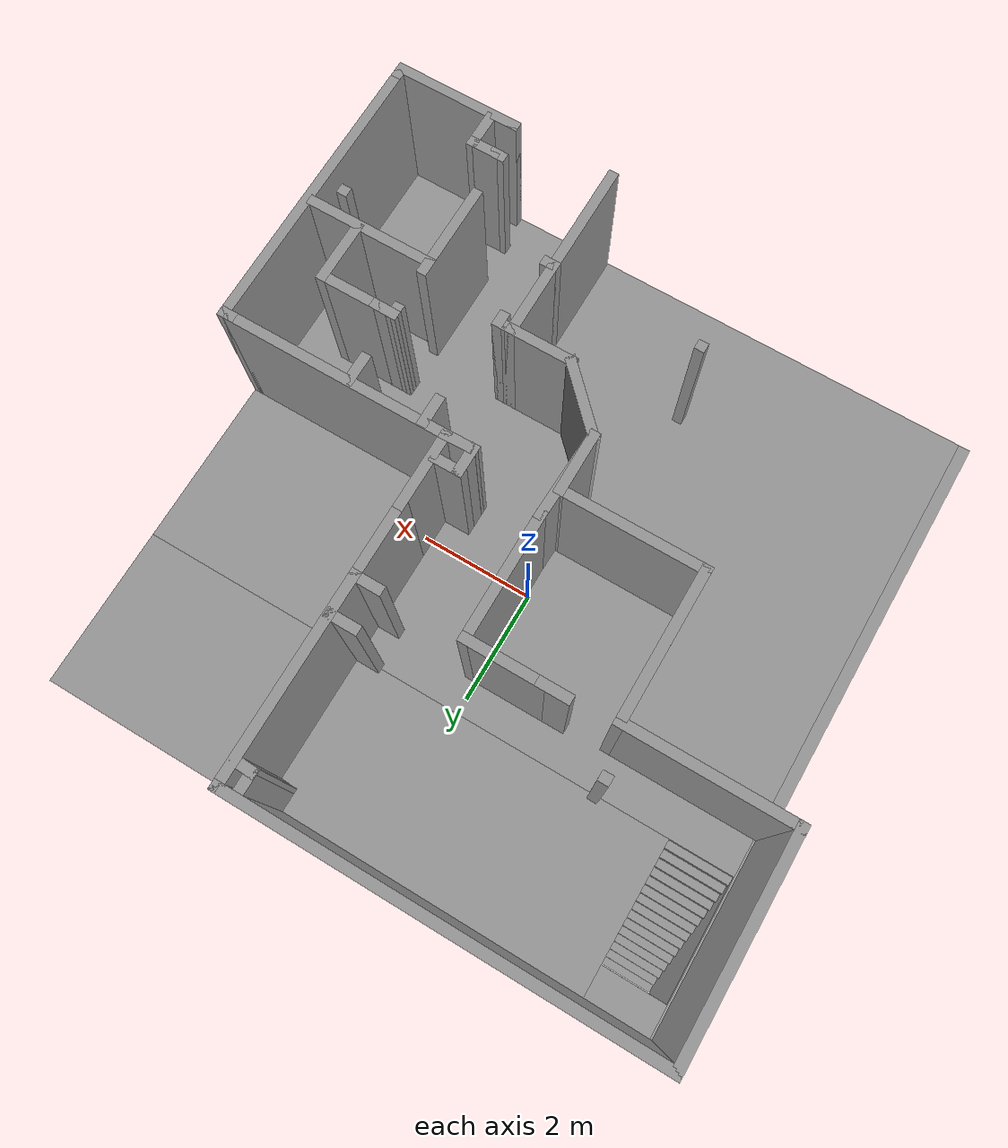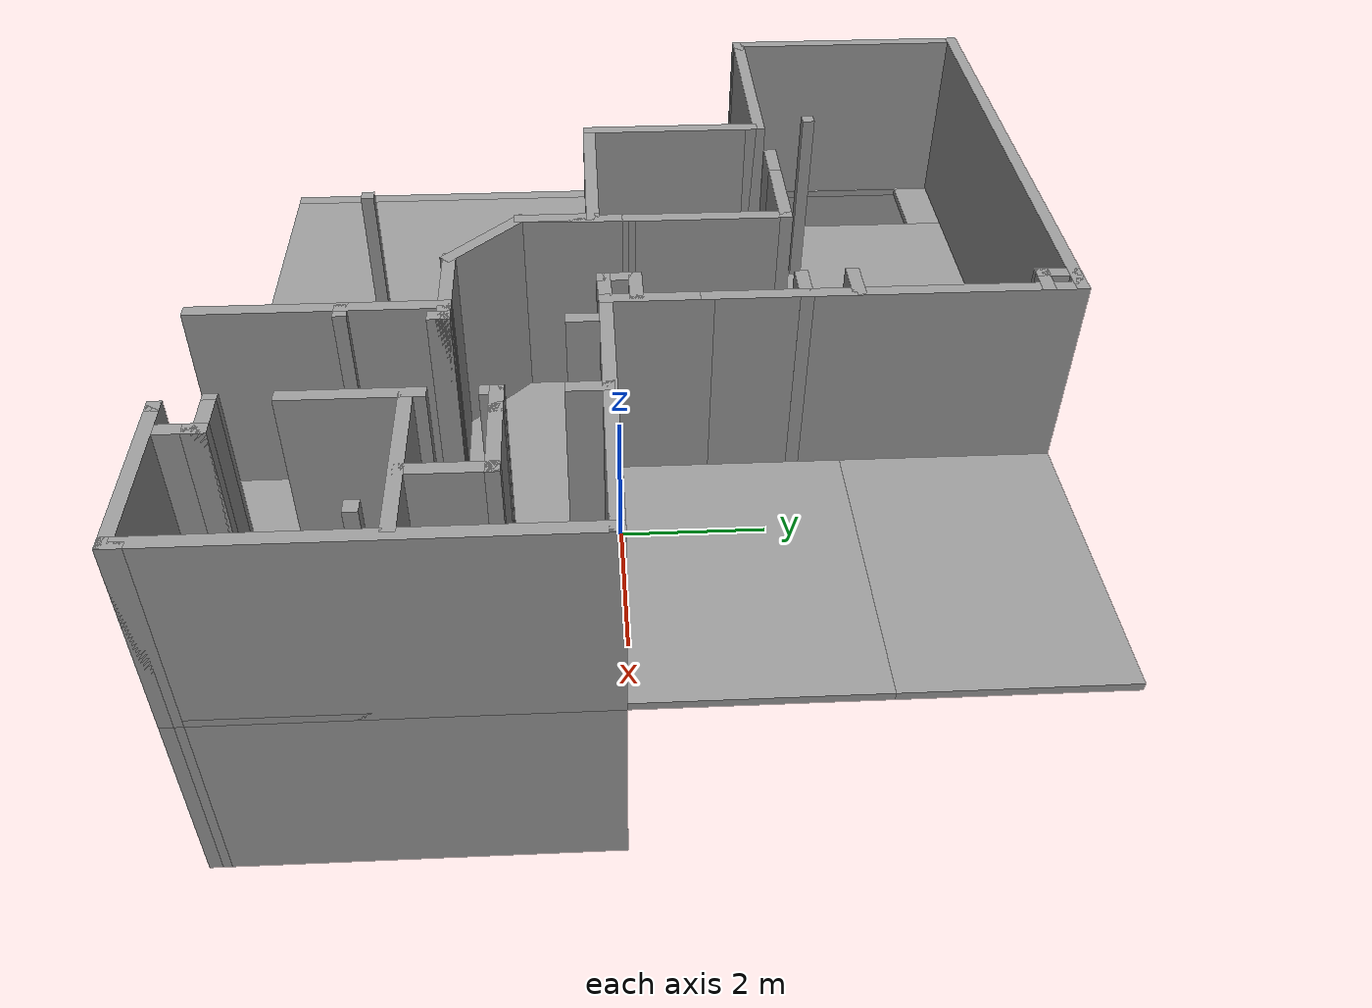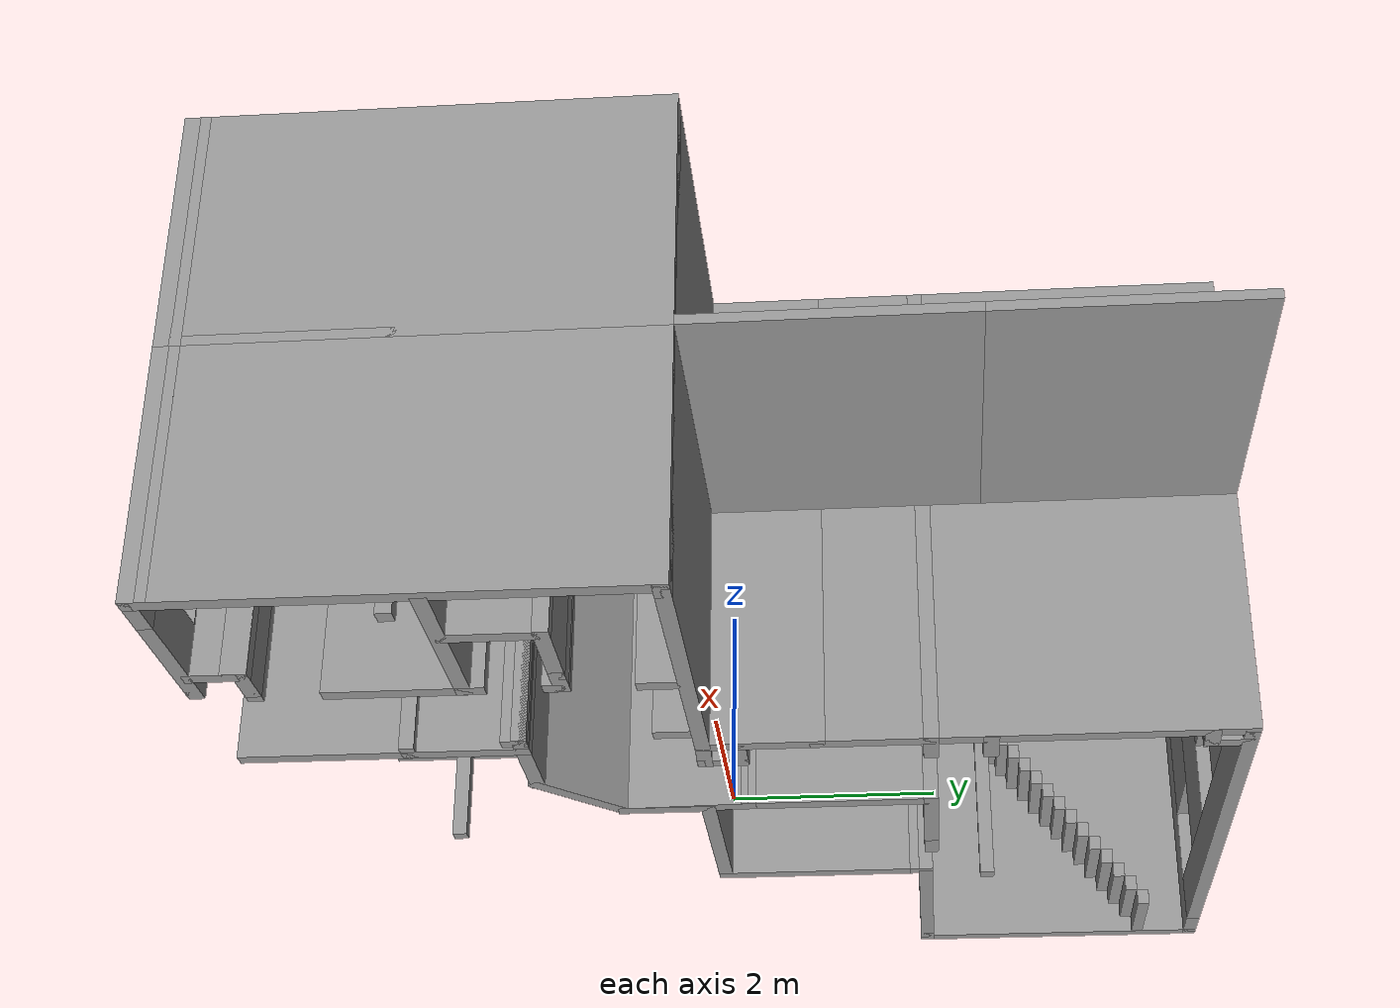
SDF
<?xml version='1.0'?>
<sdf version='1.6'>
  <model name='TwoStoreyBuilding'>
    <pose frame=''>-0.004073 0.180036 0 0 -0 0</pose>
    <link name='Floor_0'>
      <pose frame=''>-0 -0 2.5 0 -0 0</pose>
      <visual name='Floor_0_Visual_0'>
        <pose frame=''>-4.80983 0 0.05 0 -0 0</pose>
        <geometry>
          <box>
            <size>0.180349 9.8 0.1</size>
          </box>
        </geometry>
        <material>
          <script>
            <uri>file://media/materials/scripts/gazebo.material</uri>
            <name>Gazebo/Grey</name>
          </script>
          <ambient>1 1 1 1</ambient>
        </material>
        <meta>
          <layer>1</layer>
        </meta>
      </visual>
      <collision name='Floor_0_Collision_0'>
        <geometry>
          <box>
            <size>0.180349 9.8 0.1</size>
          </box>
        </geometry>
        <pose frame=''>-4.80983 0 0.05 0 -0 0</pose>
      </collision>
      <visual name='Floor_0_Visual_1'>
        <pose frame=''>0.090174 -1.26072 0.05 0 -0 0</pose>
        <geometry>
          <box>
            <size>9.61965 7.27856 0.1</size>
          </box>
        </geometry>
        <material>
          <script>
            <uri>file://media/materials/scripts/gazebo.material</uri>
            <name>Gazebo/Grey</name>
          </script>
          <ambient>1 1 1 1</ambient>
        </material>
        <meta>
          <layer>1</layer>
        </meta>
      </visual>
      <collision name='Floor_0_Collision_1'>
        <geometry>
          <box>
            <size>9.61965 7.27856 0.1</size>
          </box>
        </geometry>
        <pose frame=''>0.090174 -1.26072 0.05 0 -0 0</pose>
      </collision>
      <visual name='Floor_0_Visual_2'>
        <pose frame=''>0.590174 3.63928 0.05 0 -0 0</pose>
        <geometry>
          <box>
            <size>8.61965 2.52144 0.1</size>
          </box>
        </geometry>
        <material>
          <script>
            <uri>file://media/materials/scripts/gazebo.material</uri>
            <name>Gazebo/Grey</name>
          </script>
          <ambient>1 1 1 1</ambient>
        </material>
        <meta>
          <layer>1</layer>
        </meta>
      </visual>
      <collision name='Floor_0_Collision_2'>
        <geometry>
          <box>
            <size>8.61965 2.52144 0.1</size>
          </box>
        </geometry>
        <pose frame=''>0.590174 3.63928 0.05 0 -0 0</pose>
      </collision>
      <visual name='Floor_0_Visual_3'>
        <pose frame=''>-4.21965 4.58311 0.05 0 -0 0</pose>
        <geometry>
          <box>
            <size>1 0.633786 0.1</size>
          </box>
        </geometry>
        <material>
          <script>
            <uri>file://media/materials/scripts/gazebo.material</uri>
            <name>Gazebo/Grey</name>
          </script>
          <ambient>1 1 1 1</ambient>
        </material>
        <meta>
          <layer>1</layer>
        </meta>
      </visual>
      <collision name='Floor_0_Collision_3'>
        <geometry>
          <box>
            <size>1 0.633786 0.1</size>
          </box>
        </geometry>
        <pose frame=''>-4.21965 4.58311 0.05 0 -0 0</pose>
      </collision>
    </link>
    <link name='Stairs_1'>
      <visual name='Stairs_1_Visual_0'>
        <pose frame=''>-4.21965 4.20329 0.083333 0 -0 0</pose>
        <geometry>
          <box>
            <size>1 0.125844 0.166667</size>
          </box>
        </geometry>
        <material>
          <script>
            <uri>file://media/materials/scripts/gazebo.material</uri>
            <name>Gazebo/Grey</name>
          </script>
          <ambient>1 1 1 1</ambient>
        </material>
        <meta>
          <layer>0</layer>
        </meta>
      </visual>
      <collision name='Stairs_1_Collision_0'>
        <geometry>
          <box>
            <size>1 0.125844 0.166667</size>
          </box>
        </geometry>
        <pose frame=''>-4.21965 4.20329 0.083333 0 -0 0</pose>
      </collision>
      <visual name='Stairs_1_Visual_1'>
        <pose frame=''>-4.21965 4.07745 0.25 0 -0 0</pose>
        <geometry>
          <box>
            <size>1 0.125844 0.166667</size>
          </box>
        </geometry>
        <material>
          <script>
            <uri>file://media/materials/scripts/gazebo.material</uri>
            <name>Gazebo/Grey</name>
          </script>
          <ambient>1 1 1 1</ambient>
        </material>
        <meta>
          <layer>0</layer>
        </meta>
      </visual>
      <collision name='Stairs_1_Collision_1'>
        <geometry>
          <box>
            <size>1 0.125844 0.166667</size>
          </box>
        </geometry>
        <pose frame=''>-4.21965 4.07745 0.25 0 -0 0</pose>
      </collision>
      <visual name='Stairs_1_Visual_2'>
        <pose frame=''>-4.21965 3.9516 0.416667 0 -0 0</pose>
        <geometry>
          <box>
            <size>1 0.125844 0.166667</size>
          </box>
        </geometry>
        <material>
          <script>
            <uri>file://media/materials/scripts/gazebo.material</uri>
            <name>Gazebo/Grey</name>
          </script>
          <ambient>1 1 1 1</ambient>
        </material>
        <meta>
          <layer>0</layer>
        </meta>
      </visual>
      <collision name='Stairs_1_Collision_2'>
        <geometry>
          <box>
            <size>1 0.125844 0.166667</size>
          </box>
        </geometry>
        <pose frame=''>-4.21965 3.9516 0.416667 0 -0 0</pose>
      </collision>
      <visual name='Stairs_1_Visual_3'>
        <pose frame=''>-4.21965 3.82576 0.583333 0 -0 0</pose>
        <geometry>
          <box>
            <size>1 0.125844 0.166667</size>
          </box>
        </geometry>
        <material>
          <script>
            <uri>file://media/materials/scripts/gazebo.material</uri>
            <name>Gazebo/Grey</name>
          </script>
          <ambient>1 1 1 1</ambient>
        </material>
        <meta>
          <layer>0</layer>
        </meta>
      </visual>
      <collision name='Stairs_1_Collision_3'>
        <geometry>
          <box>
            <size>1 0.125844 0.166667</size>
          </box>
        </geometry>
        <pose frame=''>-4.21965 3.82576 0.583333 0 -0 0</pose>
      </collision>
      <visual name='Stairs_1_Visual_4'>
        <pose frame=''>-4.21965 3.69992 0.75 0 -0 0</pose>
        <geometry>
          <box>
            <size>1 0.125844 0.166667</size>
          </box>
        </geometry>
        <material>
          <script>
            <uri>file://media/materials/scripts/gazebo.material</uri>
            <name>Gazebo/Grey</name>
          </script>
          <ambient>1 1 1 1</ambient>
        </material>
        <meta>
          <layer>0</layer>
        </meta>
      </visual>
      <collision name='Stairs_1_Collision_4'>
        <geometry>
          <box>
            <size>1 0.125844 0.166667</size>
          </box>
        </geometry>
        <pose frame=''>-4.21965 3.69992 0.75 0 -0 0</pose>
      </collision>
      <visual name='Stairs_1_Visual_5'>
        <pose frame=''>-4.21965 3.57407 0.916667 0 -0 0</pose>
        <geometry>
          <box>
            <size>1 0.125844 0.166667</size>
          </box>
        </geometry>
        <material>
          <script>
            <uri>file://media/materials/scripts/gazebo.material</uri>
            <name>Gazebo/Grey</name>
          </script>
          <ambient>1 1 1 1</ambient>
        </material>
        <meta>
          <layer>0</layer>
        </meta>
      </visual>
      <collision name='Stairs_1_Collision_5'>
        <geometry>
          <box>
            <size>1 0.125844 0.166667</size>
          </box>
        </geometry>
        <pose frame=''>-4.21965 3.57407 0.916667 0 -0 0</pose>
      </collision>
      <visual name='Stairs_1_Visual_6'>
        <pose frame=''>-4.21965 3.44823 1.08333 0 -0 0</pose>
        <geometry>
          <box>
            <size>1 0.125844 0.166667</size>
          </box>
        </geometry>
        <material>
          <script>
            <uri>file://media/materials/scripts/gazebo.material</uri>
            <name>Gazebo/Grey</name>
          </script>
          <ambient>1 1 1 1</ambient>
        </material>
        <meta>
          <layer>0</layer>
        </meta>
      </visual>
      <collision name='Stairs_1_Collision_6'>
        <geometry>
          <box>
            <size>1 0.125844 0.166667</size>
          </box>
        </geometry>
        <pose frame=''>-4.21965 3.44823 1.08333 0 -0 0</pose>
      </collision>
      <visual name='Stairs_1_Visual_7'>
        <pose frame=''>-4.21965 3.32239 1.25 0 -0 0</pose>
        <geometry>
          <box>
            <size>1 0.125844 0.166667</size>
          </box>
        </geometry>
        <material>
          <script>
            <uri>file://media/materials/scripts/gazebo.material</uri>
            <name>Gazebo/Grey</name>
          </script>
          <ambient>1 1 1 1</ambient>
        </material>
        <meta>
          <layer>0</layer>
        </meta>
      </visual>
      <collision name='Stairs_1_Collision_7'>
        <geometry>
          <box>
            <size>1 0.125844 0.166667</size>
          </box>
        </geometry>
        <pose frame=''>-4.21965 3.32239 1.25 0 -0 0</pose>
      </collision>
      <visual name='Stairs_1_Visual_8'>
        <pose frame=''>-4.21965 3.19654 1.41667 0 -0 0</pose>
        <geometry>
          <box>
            <size>1 0.125844 0.166667</size>
          </box>
        </geometry>
        <material>
          <script>
            <uri>file://media/materials/scripts/gazebo.material</uri>
            <name>Gazebo/Grey</name>
          </script>
          <ambient>1 1 1 1</ambient>
        </material>
        <meta>
          <layer>0</layer>
        </meta>
      </visual>
      <collision name='Stairs_1_Collision_8'>
        <geometry>
          <box>
            <size>1 0.125844 0.166667</size>
          </box>
        </geometry>
        <pose frame=''>-4.21965 3.19654 1.41667 0 -0 0</pose>
      </collision>
      <visual name='Stairs_1_Visual_9'>
        <pose frame=''>-4.21965 3.0707 1.58333 0 -0 0</pose>
        <geometry>
          <box>
            <size>1 0.125844 0.166667</size>
          </box>
        </geometry>
        <material>
          <script>
            <uri>file://media/materials/scripts/gazebo.material</uri>
            <name>Gazebo/Grey</name>
          </script>
          <ambient>1 1 1 1</ambient>
        </material>
        <meta>
          <layer>0</layer>
        </meta>
      </visual>
      <collision name='Stairs_1_Collision_9'>
        <geometry>
          <box>
            <size>1 0.125844 0.166667</size>
          </box>
        </geometry>
        <pose frame=''>-4.21965 3.0707 1.58333 0 -0 0</pose>
      </collision>
      <visual name='Stairs_1_Visual_10'>
        <pose frame=''>-4.21965 2.94485 1.75 0 -0 0</pose>
        <geometry>
          <box>
            <size>1 0.125844 0.166667</size>
          </box>
        </geometry>
        <material>
          <script>
            <uri>file://media/materials/scripts/gazebo.material</uri>
            <name>Gazebo/Grey</name>
          </script>
          <ambient>1 1 1 1</ambient>
        </material>
        <meta>
          <layer>0</layer>
        </meta>
      </visual>
      <collision name='Stairs_1_Collision_10'>
        <geometry>
          <box>
            <size>1 0.125844 0.166667</size>
          </box>
        </geometry>
        <pose frame=''>-4.21965 2.94485 1.75 0 -0 0</pose>
      </collision>
      <visual name='Stairs_1_Visual_11'>
        <pose frame=''>-4.21965 2.81901 1.91667 0 -0 0</pose>
        <geometry>
          <box>
            <size>1 0.125844 0.166667</size>
          </box>
        </geometry>
        <material>
          <script>
            <uri>file://media/materials/scripts/gazebo.material</uri>
            <name>Gazebo/Grey</name>
          </script>
          <ambient>1 1 1 1</ambient>
        </material>
        <meta>
          <layer>0</layer>
        </meta>
      </visual>
      <collision name='Stairs_1_Collision_11'>
        <geometry>
          <box>
            <size>1 0.125844 0.166667</size>
          </box>
        </geometry>
        <pose frame=''>-4.21965 2.81901 1.91667 0 -0 0</pose>
      </collision>
      <visual name='Stairs_1_Visual_12'>
        <pose frame=''>-4.21965 2.69317 2.08333 0 -0 0</pose>
        <geometry>
          <box>
            <size>1 0.125844 0.166667</size>
          </box>
        </geometry>
        <material>
          <script>
            <uri>file://media/materials/scripts/gazebo.material</uri>
            <name>Gazebo/Grey</name>
          </script>
          <ambient>1 1 1 1</ambient>
        </material>
        <meta>
          <layer>0</layer>
        </meta>
      </visual>
      <collision name='Stairs_1_Collision_12'>
        <geometry>
          <box>
            <size>1 0.125844 0.166667</size>
          </box>
        </geometry>
        <pose frame=''>-4.21965 2.69317 2.08333 0 -0 0</pose>
      </collision>
      <visual name='Stairs_1_Visual_13'>
        <pose frame=''>-4.21965 2.56732 2.25 0 -0 0</pose>
        <geometry>
          <box>
            <size>1 0.125844 0.166667</size>
          </box>
        </geometry>
        <material>
          <script>
            <uri>file://media/materials/scripts/gazebo.material</uri>
            <name>Gazebo/Grey</name>
          </script>
          <ambient>1 1 1 1</ambient>
        </material>
        <meta>
          <layer>0</layer>
        </meta>
      </visual>
      <collision name='Stairs_1_Collision_13'>
        <geometry>
          <box>
            <size>1 0.125844 0.166667</size>
          </box>
        </geometry>
        <pose frame=''>-4.21965 2.56732 2.25 0 -0 0</pose>
      </collision>
      <visual name='Stairs_1_Visual_14'>
        <pose frame=''>-4.21965 2.44148 2.41667 0 -0 0</pose>
        <geometry>
          <box>
            <size>1 0.125844 0.166667</size>
          </box>
        </geometry>
        <material>
          <script>
            <uri>file://media/materials/scripts/gazebo.material</uri>
            <name>Gazebo/Grey</name>
          </script>
          <ambient>1 1 1 1</ambient>
        </material>
        <meta>
          <layer>0</layer>
        </meta>
      </visual>
      <collision name='Stairs_1_Collision_14'>
        <geometry>
          <box>
            <size>1 0.125844 0.166667</size>
          </box>
        </geometry>
        <pose frame=''>-4.21965 2.44148 2.41667 0 -0 0</pose>
      </collision>
    </link>
    <link name='Wall_10'>
      <collision name='Wall_10_Collision'>
        <geometry>
          <box>
            <size>0.25 0.15 2.5</size>
          </box>
        </geometry>
        <pose frame=''>0 0 1.25 0 -0 0</pose>
      </collision>
      <visual name='Wall_10_Visual'>
        <pose frame=''>0 0 1.25 0 -0 0</pose>
        <geometry>
          <box>
            <size>0.25 0.15 2.5</size>
          </box>
        </geometry>
        <material>
          <script>
            <uri>file://media/materials/scripts/gazebo.material</uri>
            <name>Gazebo/Grey</name>
          </script>
          <ambient>1 1 1 1</ambient>
        </material>
        <meta>
          <layer>0</layer>
        </meta>
      </visual>
      <pose frame=''>1.55282 -2.10282 0 0 -0 0</pose>
    </link>
    <link name='Wall_100'>
      <collision name='Wall_100_Collision'>
        <geometry>
          <box>
            <size>3.25 0.15 2.5</size>
          </box>
        </geometry>
        <pose frame=''>0 0 1.25 0 -0 0</pose>
      </collision>
      <visual name='Wall_100_Visual'>
        <pose frame=''>0 0 1.25 0 -0 0</pose>
        <geometry>
          <box>
            <size>3.25 0.15 2.5</size>
          </box>
        </geometry>
        <material>
          <script>
            <uri>file://media/materials/scripts/gazebo.material</uri>
            <name>Gazebo/Grey</name>
          </script>
          <ambient>1 1 1 1</ambient>
        </material>
        <meta>
          <layer>1</layer>
        </meta>
      </visual>
      <pose frame=''>-4.825 3.275 2.5 0 -0 1.5708</pose>
    </link>
    <link name='Wall_101'>
      <collision name='Wall_101_Collision'>
        <geometry>
          <box>
            <size>6.25 0.15 2.5</size>
          </box>
        </geometry>
        <pose frame=''>0 0 1.25 0 -0 0</pose>
      </collision>
      <visual name='Wall_101_Visual'>
        <pose frame=''>0 0 1.25 0 -0 0</pose>
        <geometry>
          <box>
            <size>6.25 0.15 2.5</size>
          </box>
        </geometry>
        <material>
          <script>
            <uri>file://media/materials/scripts/gazebo.material</uri>
            <name>Gazebo/Grey</name>
          </script>
          <ambient>1 1 1 1</ambient>
        </material>
        <meta>
          <layer>1</layer>
        </meta>
      </visual>
      <pose frame=''>-1.775 4.825 2.5 0 -0 0</pose>
    </link>
    <link name='Wall_102'>
      <collision name='Wall_102_Collision'>
        <geometry>
          <box>
            <size>0.25 0.15 2.5</size>
          </box>
        </geometry>
        <pose frame=''>0 0 1.25 0 -0 0</pose>
      </collision>
      <visual name='Wall_102_Visual'>
        <pose frame=''>0 0 1.25 0 -0 0</pose>
        <geometry>
          <box>
            <size>0.25 0.15 2.5</size>
          </box>
        </geometry>
        <material>
          <script>
            <uri>file://media/materials/scripts/gazebo.material</uri>
            <name>Gazebo/Grey</name>
          </script>
          <ambient>1 1 1 1</ambient>
        </material>
        <meta>
          <layer>1</layer>
        </meta>
      </visual>
      <pose frame=''>1.325 4.825 2.5 0 -0 0</pose>
    </link>
    <link name='Wall_103'>
      <collision name='Wall_103_Collision'>
        <geometry>
          <box>
            <size>4.25 0.15 2.5</size>
          </box>
        </geometry>
        <pose frame=''>0 0 1.25 0 -0 0</pose>
      </collision>
      <visual name='Wall_103_Visual'>
        <pose frame=''>0 0 1.25 0 -0 0</pose>
        <geometry>
          <box>
            <size>4.25 0.15 2.5</size>
          </box>
        </geometry>
        <material>
          <script>
            <uri>file://media/materials/scripts/gazebo.material</uri>
            <name>Gazebo/Grey</name>
          </script>
          <ambient>1 1 1 1</ambient>
        </material>
        <meta>
          <layer>1</layer>
        </meta>
      </visual>
      <pose frame=''>1.375 2.775 2.5 0 -0 -1.5708</pose>
    </link>
    <link name='Wall_104'>
      <collision name='Wall_104_Collision'>
        <geometry>
          <box>
            <size>1.25 0.15 2.5</size>
          </box>
        </geometry>
        <pose frame=''>0 0 1.25 0 -0 0</pose>
      </collision>
      <visual name='Wall_104_Visual'>
        <pose frame=''>0 0 1.25 0 -0 0</pose>
        <geometry>
          <box>
            <size>1.25 0.15 2.5</size>
          </box>
        </geometry>
        <material>
          <script>
            <uri>file://media/materials/scripts/gazebo.material</uri>
            <name>Gazebo/Grey</name>
          </script>
          <ambient>1 1 1 1</ambient>
        </material>
        <meta>
          <layer>1</layer>
        </meta>
      </visual>
      <pose frame=''>1.375 0.175 2.5 0 -0 -1.5708</pose>
    </link>
    <link name='Wall_105'>
      <collision name='Wall_105_Collision'>
        <geometry>
          <box>
            <size>3.5 0.15 2.5</size>
          </box>
        </geometry>
        <pose frame=''>0 0 1.25 0 -0 0</pose>
      </collision>
      <visual name='Wall_105_Visual'>
        <pose frame=''>0 0 1.25 0 -0 0</pose>
        <geometry>
          <box>
            <size>3.5 0.15 2.5</size>
          </box>
        </geometry>
        <material>
          <script>
            <uri>file://media/materials/scripts/gazebo.material</uri>
            <name>Gazebo/Grey</name>
          </script>
          <ambient>1 1 1 1</ambient>
        </material>
        <meta>
          <layer>1</layer>
        </meta>
      </visual>
      <pose frame=''>3.05 -0.375 2.5 0 -0 0</pose>
    </link>
    <link name='Wall_106'>
      <collision name='Wall_106_Collision'>
        <geometry>
          <box>
            <size>0.25 0.15 2.5</size>
          </box>
        </geometry>
        <pose frame=''>0 0 1.25 0 -0 0</pose>
      </collision>
      <visual name='Wall_106_Visual'>
        <pose frame=''>0 0 1.25 0 -0 0</pose>
        <geometry>
          <box>
            <size>0.25 0.15 2.5</size>
          </box>
        </geometry>
        <material>
          <script>
            <uri>file://media/materials/scripts/gazebo.material</uri>
            <name>Gazebo/Grey</name>
          </script>
          <ambient>1 1 1 1</ambient>
        </material>
        <meta>
          <layer>1</layer>
        </meta>
      </visual>
      <pose frame=''>4.775 -0.375 2.5 0 -0 0</pose>
    </link>
    <link name='Wall_107'>
      <collision name='Wall_107_Collision'>
        <geometry>
          <box>
            <size>4.5 0.15 2.5</size>
          </box>
        </geometry>
        <pose frame=''>0 0 1.25 0 -0 0</pose>
      </collision>
      <visual name='Wall_107_Visual'>
        <pose frame=''>0 0 1.25 0 -0 0</pose>
        <geometry>
          <box>
            <size>4.5 0.15 2.5</size>
          </box>
        </geometry>
        <material>
          <script>
            <uri>file://media/materials/scripts/gazebo.material</uri>
            <name>Gazebo/Grey</name>
          </script>
          <ambient>1 1 1 1</ambient>
        </material>
        <meta>
          <layer>1</layer>
        </meta>
      </visual>
      <pose frame=''>4.825 -2.55 2.5 0 -0 -1.5708</pose>
    </link>
    <link name='Wall_108'>
      <collision name='Wall_108_Collision'>
        <geometry>
          <box>
            <size>0.25 0.15 2.5</size>
          </box>
        </geometry>
        <pose frame=''>0 0 1.25 0 -0 0</pose>
      </collision>
      <visual name='Wall_108_Visual'>
        <pose frame=''>0 0 1.25 0 -0 0</pose>
        <geometry>
          <box>
            <size>0.25 0.15 2.5</size>
          </box>
        </geometry>
        <material>
          <script>
            <uri>file://media/materials/scripts/gazebo.material</uri>
            <name>Gazebo/Grey</name>
          </script>
          <ambient>1 1 1 1</ambient>
        </material>
        <meta>
          <layer>1</layer>
        </meta>
      </visual>
      <pose frame=''>4.825 -4.775 2.5 0 -0 -1.5708</pose>
    </link>
    <link name='Wall_109'>
      <collision name='Wall_109_Collision'>
        <geometry>
          <box>
            <size>2 0.15 2.5</size>
          </box>
        </geometry>
        <pose frame=''>0 0 1.25 0 -0 0</pose>
      </collision>
      <visual name='Wall_109_Visual'>
        <pose frame=''>0 0 1.25 0 -0 0</pose>
        <geometry>
          <box>
            <size>2 0.15 2.5</size>
          </box>
        </geometry>
        <material>
          <script>
            <uri>file://media/materials/scripts/gazebo.material</uri>
            <name>Gazebo/Grey</name>
          </script>
          <ambient>1 1 1 1</ambient>
        </material>
        <meta>
          <layer>1</layer>
        </meta>
      </visual>
      <pose frame=''>3.9 -4.825 2.5 0 -0 3.14159</pose>
    </link>
    <link name='Wall_11'>
      <collision name='Wall_11_Collision'>
        <geometry>
          <box>
            <size>0.25 0.15 2.5</size>
          </box>
        </geometry>
        <pose frame=''>0 0 1.25 0 -0 0</pose>
      </collision>
      <visual name='Wall_11_Visual'>
        <pose frame=''>0 0 1.25 0 -0 0</pose>
        <geometry>
          <box>
            <size>0.25 0.15 2.5</size>
          </box>
        </geometry>
        <material>
          <script>
            <uri>file://media/materials/scripts/gazebo.material</uri>
            <name>Gazebo/Grey</name>
          </script>
          <ambient>1 1 1 1</ambient>
        </material>
        <meta>
          <layer>0</layer>
        </meta>
      </visual>
      <pose frame=''>1.60282 -2.15282 0 0 -0 -1.5708</pose>
    </link>
    <link name='Wall_110'>
      <collision name='Wall_110_Collision'>
        <geometry>
          <box>
            <size>0.15 0.15 2.5</size>
          </box>
        </geometry>
        <pose frame=''>0 0 1.25 0 -0 0</pose>
      </collision>
      <visual name='Wall_110_Visual'>
        <pose frame=''>0 0 1.25 0 -0 0</pose>
        <geometry>
          <box>
            <size>0.15 0.15 2.5</size>
          </box>
        </geometry>
        <material>
          <script>
            <uri>file://media/materials/scripts/gazebo.material</uri>
            <name>Gazebo/Grey</name>
          </script>
          <ambient>1 1 1 1</ambient>
        </material>
        <meta>
          <layer>1</layer>
        </meta>
      </visual>
      <pose frame=''>2.975 -4.825 2.5 0 -0 0</pose>
    </link>
    <link name='Wall_111'>
      <collision name='Wall_111_Collision'>
        <geometry>
          <box>
            <size>0.5 0.15 2.5</size>
          </box>
        </geometry>
        <pose frame=''>0 0 1.25 0 -0 0</pose>
      </collision>
      <visual name='Wall_111_Visual'>
        <pose frame=''>0 0 1.25 0 -0 0</pose>
        <geometry>
          <box>
            <size>0.5 0.15 2.5</size>
          </box>
        </geometry>
        <material>
          <script>
            <uri>file://media/materials/scripts/gazebo.material</uri>
            <name>Gazebo/Grey</name>
          </script>
          <ambient>1 1 1 1</ambient>
        </material>
        <meta>
          <layer>1</layer>
        </meta>
      </visual>
      <pose frame=''>3.33055 -4.57949 2.5 0 -0 1.5708</pose>
    </link>
    <link name='Wall_112'>
      <collision name='Wall_112_Collision'>
        <geometry>
          <box>
            <size>0.25 0.15 2.5</size>
          </box>
        </geometry>
        <pose frame=''>0 0 1.25 0 -0 0</pose>
      </collision>
      <visual name='Wall_112_Visual'>
        <pose frame=''>0 0 1.25 0 -0 0</pose>
        <geometry>
          <box>
            <size>0.25 0.15 2.5</size>
          </box>
        </geometry>
        <material>
          <script>
            <uri>file://media/materials/scripts/gazebo.material</uri>
            <name>Gazebo/Grey</name>
          </script>
          <ambient>1 1 1 1</ambient>
        </material>
        <meta>
          <layer>1</layer>
        </meta>
      </visual>
      <pose frame=''>3.33055 -4.35449 2.5 0 -0 1.5708</pose>
    </link>
    <link name='Wall_113'>
      <collision name='Wall_113_Collision'>
        <geometry>
          <box>
            <size>0.5 0.15 2.5</size>
          </box>
        </geometry>
        <pose frame=''>0 0 1.25 0 -0 0</pose>
      </collision>
      <visual name='Wall_113_Visual'>
        <pose frame=''>0 0 1.25 0 -0 0</pose>
        <geometry>
          <box>
            <size>0.5 0.15 2.5</size>
          </box>
        </geometry>
        <material>
          <script>
            <uri>file://media/materials/scripts/gazebo.material</uri>
            <name>Gazebo/Grey</name>
          </script>
          <ambient>1 1 1 1</ambient>
        </material>
        <meta>
          <layer>1</layer>
        </meta>
      </visual>
      <pose frame=''>3.15555 -4.30449 2.5 0 -0 3.14159</pose>
    </link>
    <link name='Wall_114'>
      <collision name='Wall_114_Collision'>
        <geometry>
          <box>
            <size>0.25 0.15 2.5</size>
          </box>
        </geometry>
        <pose frame=''>0 0 1.25 0 -0 0</pose>
      </collision>
      <visual name='Wall_114_Visual'>
        <pose frame=''>0 0 1.25 0 -0 0</pose>
        <geometry>
          <box>
            <size>0.25 0.15 2.5</size>
          </box>
        </geometry>
        <material>
          <script>
            <uri>file://media/materials/scripts/gazebo.material</uri>
            <name>Gazebo/Grey</name>
          </script>
          <ambient>1 1 1 1</ambient>
        </material>
        <meta>
          <layer>1</layer>
        </meta>
      </visual>
      <pose frame=''>2.93055 -4.30449 2.5 0 -0 3.14159</pose>
    </link>
    <link name='Wall_115'>
      <collision name='Wall_115_Collision'>
        <geometry>
          <box>
            <size>1.5 0.15 2.5</size>
          </box>
        </geometry>
        <pose frame=''>0 0 1.25 0 -0 0</pose>
      </collision>
      <visual name='Wall_115_Visual'>
        <pose frame=''>0 0 1.25 0 -0 0</pose>
        <geometry>
          <box>
            <size>1.5 0.15 2.5</size>
          </box>
        </geometry>
        <material>
          <script>
            <uri>file://media/materials/scripts/gazebo.material</uri>
            <name>Gazebo/Grey</name>
          </script>
          <ambient>1 1 1 1</ambient>
        </material>
        <meta>
          <layer>1</layer>
        </meta>
      </visual>
      <pose frame=''>2.87567 -2.93703 2.5 0 -0 -1.5708</pose>
    </link>
    <link name='Wall_116'>
      <collision name='Wall_116_Collision'>
        <geometry>
          <box>
            <size>2 0.15 2.5</size>
          </box>
        </geometry>
        <pose frame=''>0 0 1.25 0 -0 0</pose>
      </collision>
      <visual name='Wall_116_Visual'>
        <pose frame=''>0 0 1.25 0 -0 0</pose>
        <geometry>
          <box>
            <size>2 0.15 2.5</size>
          </box>
        </geometry>
        <material>
          <script>
            <uri>file://media/materials/scripts/gazebo.material</uri>
            <name>Gazebo/Grey</name>
          </script>
          <ambient>1 1 1 1</ambient>
        </material>
        <meta>
          <layer>1</layer>
        </meta>
      </visual>
      <pose frame=''>3.80443 -2.38985 2.5 0 -0 0</pose>
    </link>
    <link name='Wall_117'>
      <collision name='Wall_117_Collision'>
        <geometry>
          <box>
            <size>1 0.15 2.5</size>
          </box>
        </geometry>
        <pose frame=''>0 0 1.25 0 -0 0</pose>
      </collision>
      <visual name='Wall_117_Visual'>
        <pose frame=''>0 0 1.25 0 -0 0</pose>
        <geometry>
          <box>
            <size>1 0.15 2.5</size>
          </box>
        </geometry>
        <material>
          <script>
            <uri>file://media/materials/scripts/gazebo.material</uri>
            <name>Gazebo/Grey</name>
          </script>
          <ambient>1 1 1 1</ambient>
        </material>
        <meta>
          <layer>1</layer>
        </meta>
      </visual>
      <pose frame=''>3.99596 -1.92349 2.5 0 -0 1.5708</pose>
    </link>
    <link name='Wall_118'>
      <collision name='Wall_118_Collision'>
        <geometry>
          <box>
            <size>1 0.15 2.5</size>
          </box>
        </geometry>
        <pose frame=''>0 0 1.25 0 -0 0</pose>
      </collision>
      <visual name='Wall_118_Visual'>
        <pose frame=''>0 0 1.25 0 -0 0</pose>
        <geometry>
          <box>
            <size>1 0.15 2.5</size>
          </box>
        </geometry>
        <material>
          <script>
            <uri>file://media/materials/scripts/gazebo.material</uri>
            <name>Gazebo/Grey</name>
          </script>
          <ambient>1 1 1 1</ambient>
        </material>
        <meta>
          <layer>1</layer>
        </meta>
      </visual>
      <pose frame=''>3.57096 -1.49849 2.5 0 -0 3.14159</pose>
    </link>
    <link name='Wall_119'>
      <collision name='Wall_119_Collision'>
        <geometry>
          <box>
            <size>0.15 0.15 2.5</size>
          </box>
        </geometry>
        <pose frame=''>0 0 1.25 0 -0 0</pose>
      </collision>
      <visual name='Wall_119_Visual'>
        <pose frame=''>0 0 1.25 0 -0 0</pose>
        <geometry>
          <box>
            <size>0.15 0.15 2.5</size>
          </box>
        </geometry>
        <material>
          <script>
            <uri>file://media/materials/scripts/gazebo.material</uri>
            <name>Gazebo/Grey</name>
          </script>
          <ambient>1 1 1 1</ambient>
        </material>
        <meta>
          <layer>1</layer>
        </meta>
      </visual>
      <pose frame=''>3.14596 -1.49849 2.5 0 -0 0</pose>
    </link>
    <link name='Wall_120'>
      <collision name='Wall_120_Collision'>
        <geometry>
          <box>
            <size>0.416554 0.15 2.5</size>
          </box>
        </geometry>
        <pose frame=''>0 0 1.25 0 -0 0</pose>
      </collision>
      <visual name='Wall_120_Visual'>
        <pose frame=''>0 0 1.25 0 -0 0</pose>
        <geometry>
          <box>
            <size>0.416554 0.15 2.5</size>
          </box>
        </geometry>
        <material>
          <script>
            <uri>file://media/materials/scripts/gazebo.material</uri>
            <name>Gazebo/Grey</name>
          </script>
          <ambient>1 1 1 1</ambient>
        </material>
        <meta>
          <layer>1</layer>
        </meta>
      </visual>
      <pose frame=''>3.01269 -1.4968 2.5 0 -0 3.12892</pose>
    </link>
    <link name='Wall_121'>
      <collision name='Wall_121_Collision'>
        <geometry>
          <box>
            <size>0.25 0.15 2.5</size>
          </box>
        </geometry>
        <pose frame=''>0 0 1.25 0 -0 0</pose>
      </collision>
      <visual name='Wall_121_Visual'>
        <pose frame=''>0 0 1.25 0 -0 0</pose>
        <geometry>
          <box>
            <size>0.25 0.15 2.5</size>
          </box>
        </geometry>
        <material>
          <script>
            <uri>file://media/materials/scripts/gazebo.material</uri>
            <name>Gazebo/Grey</name>
          </script>
          <ambient>1 1 1 1</ambient>
        </material>
        <meta>
          <layer>1</layer>
        </meta>
      </visual>
      <pose frame=''>2.87943 -1.54512 2.5 0 -0 -1.5708</pose>
    </link>
    <link name='Wall_122'>
      <collision name='Wall_122_Collision'>
        <geometry>
          <box>
            <size>0.5 0.15 2.5</size>
          </box>
        </geometry>
        <pose frame=''>0 0 1.25 0 -0 0</pose>
      </collision>
      <visual name='Wall_122_Visual'>
        <pose frame=''>0 0 1.25 0 -0 0</pose>
        <geometry>
          <box>
            <size>0.5 0.15 2.5</size>
          </box>
        </geometry>
        <material>
          <script>
            <uri>file://media/materials/scripts/gazebo.material</uri>
            <name>Gazebo/Grey</name>
          </script>
          <ambient>1 1 1 1</ambient>
        </material>
        <meta>
          <layer>1</layer>
        </meta>
      </visual>
      <pose frame=''>2.86439 -0.57614 2.5 0 -0 -1.5708</pose>
    </link>
    <link name='Wall_123'>
      <collision name='Wall_123_Collision'>
        <geometry>
          <box>
            <size>0.5 0.15 2.5</size>
          </box>
        </geometry>
        <pose frame=''>0 0 1.25 0 -0 0</pose>
      </collision>
      <visual name='Wall_123_Visual'>
        <pose frame=''>0 0 1.25 0 -0 0</pose>
        <geometry>
          <box>
            <size>0.5 0.15 2.5</size>
          </box>
        </geometry>
        <material>
          <script>
            <uri>file://media/materials/scripts/gazebo.material</uri>
            <name>Gazebo/Grey</name>
          </script>
          <ambient>1 1 1 1</ambient>
        </material>
        <meta>
          <layer>1</layer>
        </meta>
      </visual>
      <pose frame=''>1.71402 -0.561102 2.5 0 -0 -1.5708</pose>
    </link>
    <link name='Wall_124'>
      <collision name='Wall_124_Collision'>
        <geometry>
          <box>
            <size>2 0.15 2.5</size>
          </box>
        </geometry>
        <pose frame=''>0 0 1.25 0 -0 0</pose>
      </collision>
      <visual name='Wall_124_Visual'>
        <pose frame=''>0 0 1.25 0 -0 0</pose>
        <geometry>
          <box>
            <size>2 0.15 2.5</size>
          </box>
        </geometry>
        <material>
          <script>
            <uri>file://media/materials/scripts/gazebo.material</uri>
            <name>Gazebo/Grey</name>
          </script>
          <ambient>1 1 1 1</ambient>
        </material>
        <meta>
          <layer>1</layer>
        </meta>
      </visual>
      <pose frame=''>-0.228258 0.868105 2.5 0 -0 1.5708</pose>
    </link>
    <link name='Wall_125'>
      <collision name='Wall_125_Collision'>
        <geometry>
          <box>
            <size>1.25 0.15 2.5</size>
          </box>
        </geometry>
        <pose frame=''>0 0 1.25 0 -0 0</pose>
      </collision>
      <visual name='Wall_125_Visual'>
        <pose frame=''>0 0 1.25 0 -0 0</pose>
        <geometry>
          <box>
            <size>1.25 0.15 2.5</size>
          </box>
        </geometry>
        <material>
          <script>
            <uri>file://media/materials/scripts/gazebo.material</uri>
            <name>Gazebo/Grey</name>
          </script>
          <ambient>1 1 1 1</ambient>
        </material>
        <meta>
          <layer>1</layer>
        </meta>
      </visual>
      <pose frame=''>-0.778258 1.7931 2.5 0 -0 3.14159</pose>
    </link>
    <link name='Wall_126'>
      <collision name='Wall_126_Collision'>
        <geometry>
          <box>
            <size>0.5 0.15 2.5</size>
          </box>
        </geometry>
        <pose frame=''>0 0 1.25 0 -0 0</pose>
      </collision>
      <visual name='Wall_126_Visual'>
        <pose frame=''>0 0 1.25 0 -0 0</pose>
        <geometry>
          <box>
            <size>0.5 0.15 2.5</size>
          </box>
        </geometry>
        <material>
          <script>
            <uri>file://media/materials/scripts/gazebo.material</uri>
            <name>Gazebo/Grey</name>
          </script>
          <ambient>1 1 1 1</ambient>
        </material>
        <meta>
          <layer>1</layer>
        </meta>
      </visual>
      <pose frame=''>-1.50326 1.7931 2.5 0 -0 3.14159</pose>
    </link>
    <link name='Wall_127'>
      <collision name='Wall_127_Collision'>
        <geometry>
          <box>
            <size>0.5 0.15 2.5</size>
          </box>
        </geometry>
        <pose frame=''>0 0 1.25 0 -0 0</pose>
      </collision>
      <visual name='Wall_127_Visual'>
        <pose frame=''>0 0 1.25 0 -0 0</pose>
        <geometry>
          <box>
            <size>0.5 0.15 2.5</size>
          </box>
        </geometry>
        <material>
          <script>
            <uri>file://media/materials/scripts/gazebo.material</uri>
            <name>Gazebo/Grey</name>
          </script>
          <ambient>1 1 1 1</ambient>
        </material>
        <meta>
          <layer>1</layer>
        </meta>
      </visual>
      <pose frame=''>1.20108 1.80388 2.5 0 -0 3.14159</pose>
    </link>
    <link name='Wall_128'>
      <collision name='Wall_128_Collision'>
        <geometry>
          <box>
            <size>0.5 0.15 2.5</size>
          </box>
        </geometry>
        <pose frame=''>0 0 1.25 0 -0 0</pose>
      </collision>
      <visual name='Wall_128_Visual'>
        <pose frame=''>0 0 1.25 0 -0 0</pose>
        <geometry>
          <box>
            <size>0.5 0.15 2.5</size>
          </box>
        </geometry>
        <material>
          <script>
            <uri>file://media/materials/scripts/gazebo.material</uri>
            <name>Gazebo/Grey</name>
          </script>
          <ambient>1 1 1 1</ambient>
        </material>
        <meta>
          <layer>1</layer>
        </meta>
      </visual>
      <pose frame=''>1.18136 2.37591 2.5 0 -0 3.14159</pose>
    </link>
    <link name='Wall_129'>
      <collision name='Wall_129_Collision'>
        <geometry>
          <box>
            <size>0.5 0.15 2.5</size>
          </box>
        </geometry>
        <pose frame=''>0 0 1.25 0 -0 0</pose>
      </collision>
      <visual name='Wall_129_Visual'>
        <pose frame=''>0 0 1.25 0 -0 0</pose>
        <geometry>
          <box>
            <size>0.5 0.15 2.5</size>
          </box>
        </geometry>
        <material>
          <script>
            <uri>file://media/materials/scripts/gazebo.material</uri>
            <name>Gazebo/Grey</name>
          </script>
          <ambient>1 1 1 1</ambient>
        </material>
        <meta>
          <layer>1</layer>
        </meta>
      </visual>
      <pose frame=''>1.11308 4.6403 2.5 0 -0 -1.5708</pose>
    </link>
    <link name='Wall_13'>
      <collision name='Wall_13_Collision'>
        <geometry>
          <box>
            <size>1.25 0.15 2.5</size>
          </box>
        </geometry>
        <pose frame=''>0 0 1.25 0 -0 0</pose>
      </collision>
      <visual name='Wall_13_Visual'>
        <pose frame=''>0 0 1.25 0 -0 0</pose>
        <geometry>
          <box>
            <size>1.25 0.15 2.5</size>
          </box>
        </geometry>
        <material>
          <script>
            <uri>file://media/materials/scripts/gazebo.material</uri>
            <name>Gazebo/Grey</name>
          </script>
          <ambient>1 1 1 1</ambient>
        </material>
        <meta>
          <layer>0</layer>
        </meta>
      </visual>
      <pose frame=''>1.05282 -2.10282 0 0 -0 3.14159</pose>
    </link>
    <link name='Wall_130'>
      <collision name='Wall_130_Collision'>
        <geometry>
          <box>
            <size>0.400127 0.15 2.5</size>
          </box>
        </geometry>
        <pose frame=''>0 0 1.25 0 -0 0</pose>
      </collision>
      <visual name='Wall_130_Visual'>
        <pose frame=''>0 0 1.25 0 -0 0</pose>
        <geometry>
          <box>
            <size>0.400127 0.15 2.5</size>
          </box>
        </geometry>
        <material>
          <script>
            <uri>file://media/materials/scripts/gazebo.material</uri>
            <name>Gazebo/Grey</name>
          </script>
          <ambient>1 1 1 1</ambient>
        </material>
        <meta>
          <layer>1</layer>
        </meta>
      </visual>
      <pose frame=''>1.238 4.45948 2.5 0 -0 -0.046529</pose>
    </link>
    <link name='Wall_131'>
      <collision name='Wall_131_Collision'>
        <geometry>
          <box>
            <size>0.16 0.15 2.5</size>
          </box>
        </geometry>
        <pose frame=''>0 0 1.25 0 -0 0</pose>
      </collision>
      <visual name='Wall_131_Visual'>
        <pose frame=''>0 0 1.25 0 -0 0</pose>
        <geometry>
          <box>
            <size>0.16 0.15 2.5</size>
          </box>
        </geometry>
        <material>
          <script>
            <uri>file://media/materials/scripts/gazebo.material</uri>
            <name>Gazebo/Grey</name>
          </script>
          <ambient>1 1 1 1</ambient>
        </material>
        <meta>
          <layer>1</layer>
        </meta>
      </visual>
      <pose frame=''>-2.55403 2.39774 2.5 0 -0 0</pose>
    </link>
    <link name='Wall_132'>
      <collision name='Wall_132_Collision'>
        <geometry>
          <box>
            <size>1.41897 0.15 2.5</size>
          </box>
        </geometry>
        <pose frame=''>0 0 1.25 0 -0 0</pose>
      </collision>
      <visual name='Wall_132_Visual'>
        <pose frame=''>0 0 1.25 0 -0 0</pose>
        <geometry>
          <box>
            <size>1.41897 0.15 2.5</size>
          </box>
        </geometry>
        <material>
          <script>
            <uri>file://media/materials/scripts/gazebo.material</uri>
            <name>Gazebo/Grey</name>
          </script>
          <ambient>1 1 1 1</ambient>
        </material>
        <meta>
          <layer>1</layer>
        </meta>
      </visual>
      <pose frame=''>-0.251629 -0.690948 2.5 0 -0 -1.60764</pose>
    </link>
    <link name='Wall_133'>
      <collision name='Wall_133_Collision'>
        <geometry>
          <box>
            <size>0.5 0.15 2.5</size>
          </box>
        </geometry>
        <pose frame=''>0 0 1.25 0 -0 0</pose>
      </collision>
      <visual name='Wall_133_Visual'>
        <pose frame=''>0 0 1.25 0 -0 0</pose>
        <geometry>
          <box>
            <size>0.5 0.15 2.5</size>
          </box>
        </geometry>
        <material>
          <script>
            <uri>file://media/materials/scripts/gazebo.material</uri>
            <name>Gazebo/Grey</name>
          </script>
          <ambient>1 1 1 1</ambient>
        </material>
        <meta>
          <layer>1</layer>
        </meta>
      </visual>
      <pose frame=''>1.14545 -0.037473 2.5 0 -0 3.14159</pose>
    </link>
    <link name='Wall_134'>
      <collision name='Wall_134_Collision'>
        <geometry>
          <box>
            <size>0.5 0.15 2.5</size>
          </box>
        </geometry>
        <pose frame=''>0 0 1.25 0 -0 0</pose>
      </collision>
      <visual name='Wall_134_Visual'>
        <pose frame=''>0 0 1.25 0 -0 0</pose>
        <geometry>
          <box>
            <size>0.5 0.15 2.5</size>
          </box>
        </geometry>
        <material>
          <script>
            <uri>file://media/materials/scripts/gazebo.material</uri>
            <name>Gazebo/Grey</name>
          </script>
          <ambient>1 1 1 1</ambient>
        </material>
        <meta>
          <layer>1</layer>
        </meta>
      </visual>
      <pose frame=''>0.97045 -0.212473 2.5 0 -0 -1.5708</pose>
    </link>
    <link name='Wall_135'>
      <collision name='Wall_135_Collision'>
        <geometry>
          <box>
            <size>0.554742 0.15 2.5</size>
          </box>
        </geometry>
        <pose frame=''>0 0 1.25 0 -0 0</pose>
      </collision>
      <visual name='Wall_135_Visual'>
        <pose frame=''>0 0 1.25 0 -0 0</pose>
        <geometry>
          <box>
            <size>0.554742 0.15 2.5</size>
          </box>
        </geometry>
        <material>
          <script>
            <uri>file://media/materials/scripts/gazebo.material</uri>
            <name>Gazebo/Grey</name>
          </script>
          <ambient>1 1 1 1</ambient>
        </material>
        <meta>
          <layer>1</layer>
        </meta>
      </visual>
      <pose frame=''>1.17273 -0.381237 2.5 0 -0 0.030821</pose>
    </link>
    <link name='Wall_136'>
      <collision name='Wall_136_Collision'>
        <geometry>
          <box>
            <size>0.157523 0.15 2.5</size>
          </box>
        </geometry>
        <pose frame=''>0 0 1.25 0 -0 0</pose>
      </collision>
      <visual name='Wall_136_Visual'>
        <pose frame=''>0 0 1.25 0 -0 0</pose>
        <geometry>
          <box>
            <size>0.157523 0.15 2.5</size>
          </box>
        </geometry>
        <material>
          <script>
            <uri>file://media/materials/scripts/gazebo.material</uri>
            <name>Gazebo/Grey</name>
          </script>
          <ambient>1 1 1 1</ambient>
        </material>
        <meta>
          <layer>1</layer>
        </meta>
      </visual>
      <pose frame=''>4.45997 -2.7438 2.5 0 -0 0</pose>
    </link>
    <link name='Wall_137'>
      <collision name='Wall_137_Collision'>
        <geometry>
          <box>
            <size>1.75 0.15 2.5</size>
          </box>
        </geometry>
        <pose frame=''>0 0 1.25 0 -0 0</pose>
      </collision>
      <visual name='Wall_137_Visual'>
        <pose frame=''>0 0 1.25 0 -0 0</pose>
        <geometry>
          <box>
            <size>1.75 0.15 2.5</size>
          </box>
        </geometry>
        <material>
          <script>
            <uri>file://media/materials/scripts/gazebo.material</uri>
            <name>Gazebo/Grey</name>
          </script>
          <ambient>1 1 1 1</ambient>
        </material>
        <meta>
          <layer>1</layer>
        </meta>
      </visual>
      <pose frame=''>1.40282 -4.00282 2.5 0 -0 -1.5708</pose>
    </link>
    <link name='Wall_14'>
      <collision name='Wall_14_Collision'>
        <geometry>
          <box>
            <size>1.25 0.15 2.5</size>
          </box>
        </geometry>
        <pose frame=''>0 0 1.25 0 -0 0</pose>
      </collision>
      <visual name='Wall_14_Visual'>
        <pose frame=''>0 0 1.25 0 -0 0</pose>
        <geometry>
          <box>
            <size>1.25 0.15 2.5</size>
          </box>
        </geometry>
        <material>
          <script>
            <uri>file://media/materials/scripts/gazebo.material</uri>
            <name>Gazebo/Grey</name>
          </script>
          <ambient>1 1 1 1</ambient>
        </material>
        <meta>
          <layer>0</layer>
        </meta>
      </visual>
      <pose frame=''>0.113909 -1.71391 0 0 -0 2.35619</pose>
    </link>
    <link name='Wall_15'>
      <collision name='Wall_15_Collision'>
        <geometry>
          <box>
            <size>1 0.15 2.5</size>
          </box>
        </geometry>
        <pose frame=''>0 0 1.25 0 -0 0</pose>
      </collision>
      <visual name='Wall_15_Visual'>
        <pose frame=''>0 0 1.25 0 -0 0</pose>
        <geometry>
          <box>
            <size>1 0.15 2.5</size>
          </box>
        </geometry>
        <material>
          <script>
            <uri>file://media/materials/scripts/gazebo.material</uri>
            <name>Gazebo/Grey</name>
          </script>
          <ambient>1 1 1 1</ambient>
        </material>
        <meta>
          <layer>0</layer>
        </meta>
      </visual>
      <pose frame=''>-0.275 -0.9 0 0 -0 1.5708</pose>
    </link>
    <link name='Wall_18'>
      <collision name='Wall_18_Collision'>
        <geometry>
          <box>
            <size>2.25 0.15 2.5</size>
          </box>
        </geometry>
        <pose frame=''>0 0 1.25 0 -0 0</pose>
      </collision>
      <visual name='Wall_18_Visual'>
        <pose frame=''>0 0 1.25 0 -0 0</pose>
        <geometry>
          <box>
            <size>2.25 0.15 2.5</size>
          </box>
        </geometry>
        <material>
          <script>
            <uri>file://media/materials/scripts/gazebo.material</uri>
            <name>Gazebo/Grey</name>
          </script>
          <ambient>1 1 1 1</ambient>
        </material>
        <meta>
          <layer>0</layer>
        </meta>
      </visual>
      <pose frame=''>-1.325 -0.475 0 0 -0 3.14159</pose>
    </link>
    <link name='Wall_19'>
      <collision name='Wall_19_Collision'>
        <geometry>
          <box>
            <size>2.25 0.15 2.5</size>
          </box>
        </geometry>
        <pose frame=''>0 0 1.25 0 -0 0</pose>
      </collision>
      <visual name='Wall_19_Visual'>
        <pose frame=''>0 0 1.25 0 -0 0</pose>
        <geometry>
          <box>
            <size>2.25 0.15 2.5</size>
          </box>
        </geometry>
        <material>
          <script>
            <uri>file://media/materials/scripts/gazebo.material</uri>
            <name>Gazebo/Grey</name>
          </script>
          <ambient>1 1 1 1</ambient>
        </material>
        <meta>
          <layer>0</layer>
        </meta>
      </visual>
      <pose frame=''>-2.375 0.575 0 0 -0 1.5708</pose>
    </link>
    <link name='Wall_20'>
      <collision name='Wall_20_Collision'>
        <geometry>
          <box>
            <size>0.25 0.15 2.5</size>
          </box>
        </geometry>
        <pose frame=''>0 0 1.25 0 -0 0</pose>
      </collision>
      <visual name='Wall_20_Visual'>
        <pose frame=''>0 0 1.25 0 -0 0</pose>
        <geometry>
          <box>
            <size>0.25 0.15 2.5</size>
          </box>
        </geometry>
        <material>
          <script>
            <uri>file://media/materials/scripts/gazebo.material</uri>
            <name>Gazebo/Grey</name>
          </script>
          <ambient>1 1 1 1</ambient>
        </material>
        <meta>
          <layer>0</layer>
        </meta>
      </visual>
      <pose frame=''>-2.375 1.675 0 0 -0 1.5708</pose>
    </link>
    <link name='Wall_21'>
      <collision name='Wall_21_Collision'>
        <geometry>
          <box>
            <size>2.5 0.15 2.5</size>
          </box>
        </geometry>
        <pose frame=''>0 0 1.25 0 -0 0</pose>
      </collision>
      <visual name='Wall_21_Visual'>
        <pose frame=''>0 0 1.25 0 -0 0</pose>
        <geometry>
          <box>
            <size>2.5 0.15 2.5</size>
          </box>
        </geometry>
        <material>
          <script>
            <uri>file://media/materials/scripts/gazebo.material</uri>
            <name>Gazebo/Grey</name>
          </script>
          <ambient>1 1 1 1</ambient>
        </material>
        <meta>
          <layer>0</layer>
        </meta>
      </visual>
      <pose frame=''>-3.55 1.725 0 0 -0 3.14159</pose>
    </link>
    <link name='Wall_22'>
      <collision name='Wall_22_Collision'>
        <geometry>
          <box>
            <size>0.25 0.15 2.5</size>
          </box>
        </geometry>
        <pose frame=''>0 0 1.25 0 -0 0</pose>
      </collision>
      <visual name='Wall_22_Visual'>
        <pose frame=''>0 0 1.25 0 -0 0</pose>
        <geometry>
          <box>
            <size>0.25 0.15 2.5</size>
          </box>
        </geometry>
        <material>
          <script>
            <uri>file://media/materials/scripts/gazebo.material</uri>
            <name>Gazebo/Grey</name>
          </script>
          <ambient>1 1 1 1</ambient>
        </material>
        <meta>
          <layer>0</layer>
        </meta>
      </visual>
      <pose frame=''>-4.775 1.725 0 0 -0 3.14159</pose>
    </link>
    <link name='Wall_23'>
      <collision name='Wall_23_Collision'>
        <geometry>
          <box>
            <size>3.25 0.15 2.5</size>
          </box>
        </geometry>
        <pose frame=''>0 0 1.25 0 -0 0</pose>
      </collision>
      <visual name='Wall_23_Visual'>
        <pose frame=''>0 0 1.25 0 -0 0</pose>
        <geometry>
          <box>
            <size>3.25 0.15 2.5</size>
          </box>
        </geometry>
        <material>
          <script>
            <uri>file://media/materials/scripts/gazebo.material</uri>
            <name>Gazebo/Grey</name>
          </script>
          <ambient>1 1 1 1</ambient>
        </material>
        <meta>
          <layer>0</layer>
        </meta>
      </visual>
      <pose frame=''>-4.825 3.275 0 0 -0 1.5708</pose>
    </link>
    <link name='Wall_24'>
      <pose frame=''>-1.775 4.825 0 0 -0 0</pose>
      <visual name='Wall_24_Visual_0'>
        <pose frame=''>-2.84052 0 1.25 0 -0 0</pose>
        <geometry>
          <box>
            <size>0.56895 0.15 2.5</size>
          </box>
        </geometry>
        <material>
          <script>
            <uri>file://media/materials/scripts/gazebo.material</uri>
            <name>Gazebo/Grey</name>
          </script>
          <ambient>1 1 1 1</ambient>
        </material>
        <meta>
          <layer>0</layer>
        </meta>
      </visual>
      <collision name='Wall_24_Collision_0'>
        <geometry>
          <box>
            <size>0.56895 0.15 2.5</size>
          </box>
        </geometry>
        <pose frame=''>-2.84052 0 1.25 0 -0 0</pose>
      </collision>
      <visual name='Wall_24_Visual_1'>
        <pose frame=''>0.284475 0 0.25 0 -0 0</pose>
        <geometry>
          <box>
            <size>5.68105 0.15 0.5</size>
          </box>
        </geometry>
        <material>
          <script>
            <uri>file://media/materials/scripts/gazebo.material</uri>
            <name>Gazebo/Grey</name>
          </script>
          <ambient>1 1 1 1</ambient>
        </material>
        <meta>
          <layer>0</layer>
        </meta>
      </visual>
      <collision name='Wall_24_Collision_1'>
        <geometry>
          <box>
            <size>5.68105 0.15 0.5</size>
          </box>
        </geometry>
        <pose frame=''>0.284475 0 0.25 0 -0 0</pose>
      </collision>
      <visual name='Wall_24_Visual_2'>
        <pose frame=''>-0.93452 0 1.5 0 -0 0</pose>
        <geometry>
          <box>
            <size>1.08103 0.15 2</size>
          </box>
        </geometry>
        <material>
          <script>
            <uri>file://media/materials/scripts/gazebo.material</uri>
            <name>Gazebo/Grey</name>
          </script>
          <ambient>1 1 1 1</ambient>
        </material>
        <meta>
          <layer>0</layer>
        </meta>
      </visual>
      <collision name='Wall_24_Collision_2'>
        <geometry>
          <box>
            <size>1.08103 0.15 2</size>
          </box>
        </geometry>
        <pose frame=''>-0.93452 0 1.5 0 -0 0</pose>
      </collision>
      <visual name='Wall_24_Visual_3'>
        <pose frame=''>1.18841 0 1.5 0 -0 0</pose>
        <geometry>
          <box>
            <size>1.05469 0.15 2</size>
          </box>
        </geometry>
        <material>
          <script>
            <uri>file://media/materials/scripts/gazebo.material</uri>
            <name>Gazebo/Grey</name>
          </script>
          <ambient>1 1 1 1</ambient>
        </material>
        <meta>
          <layer>0</layer>
        </meta>
      </visual>
      <collision name='Wall_24_Collision_3'>
        <geometry>
          <box>
            <size>1.05469 0.15 2</size>
          </box>
        </geometry>
        <pose frame=''>1.18841 0 1.5 0 -0 0</pose>
      </collision>
      <visual name='Wall_24_Visual_4'>
        <pose frame=''>2.94359 0 1.5 0 -0 0</pose>
        <geometry>
          <box>
            <size>0.362818 0.15 2</size>
          </box>
        </geometry>
        <material>
          <script>
            <uri>file://media/materials/scripts/gazebo.material</uri>
            <name>Gazebo/Grey</name>
          </script>
          <ambient>1 1 1 1</ambient>
        </material>
        <meta>
          <layer>0</layer>
        </meta>
      </visual>
      <collision name='Wall_24_Collision_4'>
        <geometry>
          <box>
            <size>0.362818 0.15 2</size>
          </box>
        </geometry>
        <pose frame=''>2.94359 0 1.5 0 -0 0</pose>
      </collision>
      <visual name='Wall_24_Visual_5'>
        <pose frame=''>-2.01554 0 1.9 0 -0 0</pose>
        <geometry>
          <box>
            <size>1.08101 0.15 1.2</size>
          </box>
        </geometry>
        <material>
          <script>
            <uri>file://media/materials/scripts/gazebo.material</uri>
            <name>Gazebo/Grey</name>
          </script>
          <ambient>1 1 1 1</ambient>
        </material>
        <meta>
          <layer>0</layer>
        </meta>
      </visual>
      <collision name='Wall_24_Collision_5'>
        <geometry>
          <box>
            <size>1.08101 0.15 1.2</size>
          </box>
        </geometry>
        <pose frame=''>-2.01554 0 1.9 0 -0 0</pose>
      </collision>
      <visual name='Wall_24_Visual_6'>
        <pose frame=''>0.133533 0 1.9 0 -0 0</pose>
        <geometry>
          <box>
            <size>1.05507 0.15 1.2</size>
          </box>
        </geometry>
        <material>
          <script>
            <uri>file://media/materials/scripts/gazebo.material</uri>
            <name>Gazebo/Grey</name>
          </script>
          <ambient>1 1 1 1</ambient>
        </material>
        <meta>
          <layer>0</layer>
        </meta>
      </visual>
      <collision name='Wall_24_Collision_6'>
        <geometry>
          <box>
            <size>1.05507 0.15 1.2</size>
          </box>
        </geometry>
        <pose frame=''>0.133533 0 1.9 0 -0 0</pose>
      </collision>
      <visual name='Wall_24_Visual_7'>
        <pose frame=''>2.23897 0 1.9 0 -0 0</pose>
        <geometry>
          <box>
            <size>1.04643 0.15 1.2</size>
          </box>
        </geometry>
        <material>
          <script>
            <uri>file://media/materials/scripts/gazebo.material</uri>
            <name>Gazebo/Grey</name>
          </script>
          <ambient>1 1 1 1</ambient>
        </material>
        <meta>
          <layer>0</layer>
        </meta>
      </visual>
      <collision name='Wall_24_Collision_7'>
        <geometry>
          <box>
            <size>1.04643 0.15 1.2</size>
          </box>
        </geometry>
        <pose frame=''>2.23897 0 1.9 0 -0 0</pose>
      </collision>
    </link>
    <link name='Wall_25'>
      <collision name='Wall_25_Collision'>
        <geometry>
          <box>
            <size>0.25 0.15 2.5</size>
          </box>
        </geometry>
        <pose frame=''>0 0 1.25 0 -0 0</pose>
      </collision>
      <visual name='Wall_25_Visual'>
        <pose frame=''>0 0 1.25 0 -0 0</pose>
        <geometry>
          <box>
            <size>0.25 0.15 2.5</size>
          </box>
        </geometry>
        <material>
          <script>
            <uri>file://media/materials/scripts/gazebo.material</uri>
            <name>Gazebo/Grey</name>
          </script>
          <ambient>1 1 1 1</ambient>
        </material>
        <meta>
          <layer>0</layer>
        </meta>
      </visual>
      <pose frame=''>1.325 4.825 0 0 -0 0</pose>
    </link>
    <link name='Wall_26'>
      <collision name='Wall_26_Collision'>
        <geometry>
          <box>
            <size>4.25 0.15 2.5</size>
          </box>
        </geometry>
        <pose frame=''>0 0 1.25 0 -0 0</pose>
      </collision>
      <visual name='Wall_26_Visual'>
        <pose frame=''>0 0 1.25 0 -0 0</pose>
        <geometry>
          <box>
            <size>4.25 0.15 2.5</size>
          </box>
        </geometry>
        <material>
          <script>
            <uri>file://media/materials/scripts/gazebo.material</uri>
            <name>Gazebo/Grey</name>
          </script>
          <ambient>1 1 1 1</ambient>
        </material>
        <meta>
          <layer>0</layer>
        </meta>
      </visual>
      <pose frame=''>1.375 2.775 0 0 -0 -1.5708</pose>
    </link>
    <link name='Wall_28'>
      <collision name='Wall_28_Collision'>
        <geometry>
          <box>
            <size>1.25 0.15 2.5</size>
          </box>
        </geometry>
        <pose frame=''>0 0 1.25 0 -0 0</pose>
      </collision>
      <visual name='Wall_28_Visual'>
        <pose frame=''>0 0 1.25 0 -0 0</pose>
        <geometry>
          <box>
            <size>1.25 0.15 2.5</size>
          </box>
        </geometry>
        <material>
          <script>
            <uri>file://media/materials/scripts/gazebo.material</uri>
            <name>Gazebo/Grey</name>
          </script>
          <ambient>1 1 1 1</ambient>
        </material>
        <meta>
          <layer>0</layer>
        </meta>
      </visual>
      <pose frame=''>1.375 0.175 0 0 -0 -1.5708</pose>
    </link>
    <link name='Wall_29'>
      <collision name='Wall_29_Collision'>
        <geometry>
          <box>
            <size>3.5 0.15 2.5</size>
          </box>
        </geometry>
        <pose frame=''>0 0 1.25 0 -0 0</pose>
      </collision>
      <visual name='Wall_29_Visual'>
        <pose frame=''>0 0 1.25 0 -0 0</pose>
        <geometry>
          <box>
            <size>3.5 0.15 2.5</size>
          </box>
        </geometry>
        <material>
          <script>
            <uri>file://media/materials/scripts/gazebo.material</uri>
            <name>Gazebo/Grey</name>
          </script>
          <ambient>1 1 1 1</ambient>
        </material>
        <meta>
          <layer>0</layer>
        </meta>
      </visual>
      <pose frame=''>3.05 -0.375 0 0 -0 0</pose>
    </link>
    <link name='Wall_30'>
      <collision name='Wall_30_Collision'>
        <geometry>
          <box>
            <size>0.25 0.15 2.5</size>
          </box>
        </geometry>
        <pose frame=''>0 0 1.25 0 -0 0</pose>
      </collision>
      <visual name='Wall_30_Visual'>
        <pose frame=''>0 0 1.25 0 -0 0</pose>
        <geometry>
          <box>
            <size>0.25 0.15 2.5</size>
          </box>
        </geometry>
        <material>
          <script>
            <uri>file://media/materials/scripts/gazebo.material</uri>
            <name>Gazebo/Grey</name>
          </script>
          <ambient>1 1 1 1</ambient>
        </material>
        <meta>
          <layer>0</layer>
        </meta>
      </visual>
      <pose frame=''>4.775 -0.375 0 0 -0 0</pose>
    </link>
    <link name='Wall_31'>
      <collision name='Wall_31_Collision'>
        <geometry>
          <box>
            <size>4.5 0.15 2.5</size>
          </box>
        </geometry>
        <pose frame=''>0 0 1.25 0 -0 0</pose>
      </collision>
      <visual name='Wall_31_Visual'>
        <pose frame=''>0 0 1.25 0 -0 0</pose>
        <geometry>
          <box>
            <size>4.5 0.15 2.5</size>
          </box>
        </geometry>
        <material>
          <script>
            <uri>file://media/materials/scripts/gazebo.material</uri>
            <name>Gazebo/Grey</name>
          </script>
          <ambient>1 1 1 1</ambient>
        </material>
        <meta>
          <layer>0</layer>
        </meta>
      </visual>
      <pose frame=''>4.825 -2.55 0 0 -0 -1.5708</pose>
    </link>
    <link name='Wall_32'>
      <collision name='Wall_32_Collision'>
        <geometry>
          <box>
            <size>0.25 0.15 2.5</size>
          </box>
        </geometry>
        <pose frame=''>0 0 1.25 0 -0 0</pose>
      </collision>
      <visual name='Wall_32_Visual'>
        <pose frame=''>0 0 1.25 0 -0 0</pose>
        <geometry>
          <box>
            <size>0.25 0.15 2.5</size>
          </box>
        </geometry>
        <material>
          <script>
            <uri>file://media/materials/scripts/gazebo.material</uri>
            <name>Gazebo/Grey</name>
          </script>
          <ambient>1 1 1 1</ambient>
        </material>
        <meta>
          <layer>0</layer>
        </meta>
      </visual>
      <pose frame=''>4.825 -4.775 0 0 -0 -1.5708</pose>
    </link>
    <link name='Wall_33'>
      <pose frame=''>3.9 -4.825 0 0 -0 3.14159</pose>
      <visual name='Wall_33_Visual_0'>
        <pose frame=''>-0.74257 0 1.25 0 -0 0</pose>
        <geometry>
          <box>
            <size>0.514861 0.15 2.5</size>
          </box>
        </geometry>
        <material>
          <script>
            <uri>file://media/materials/scripts/gazebo.material</uri>
            <name>Gazebo/Grey</name>
          </script>
          <ambient>1 1 1 1</ambient>
        </material>
        <meta>
          <layer>0</layer>
        </meta>
      </visual>
      <collision name='Wall_33_Collision_0'>
        <geometry>
          <box>
            <size>0.514861 0.15 2.5</size>
          </box>
        </geometry>
        <pose frame=''>-0.74257 0 1.25 0 -0 0</pose>
      </collision>
      <visual name='Wall_33_Visual_1'>
        <pose frame=''>0.25743 0 0.25 0 -0 0</pose>
        <geometry>
          <box>
            <size>1.48514 0.15 0.5</size>
          </box>
        </geometry>
        <material>
          <script>
            <uri>file://media/materials/scripts/gazebo.material</uri>
            <name>Gazebo/Grey</name>
          </script>
          <ambient>1 1 1 1</ambient>
        </material>
        <meta>
          <layer>0</layer>
        </meta>
      </visual>
      <collision name='Wall_33_Collision_1'>
        <geometry>
          <box>
            <size>1.48514 0.15 0.5</size>
          </box>
        </geometry>
        <pose frame=''>0.25743 0 0.25 0 -0 0</pose>
      </collision>
      <visual name='Wall_33_Visual_2'>
        <pose frame=''>0.736825 0 1.5 0 -0 0</pose>
        <geometry>
          <box>
            <size>0.526349 0.15 2</size>
          </box>
        </geometry>
        <material>
          <script>
            <uri>file://media/materials/scripts/gazebo.material</uri>
            <name>Gazebo/Grey</name>
          </script>
          <ambient>1 1 1 1</ambient>
        </material>
        <meta>
          <layer>0</layer>
        </meta>
      </visual>
      <collision name='Wall_33_Collision_2'>
        <geometry>
          <box>
            <size>0.526349 0.15 2</size>
          </box>
        </geometry>
        <pose frame=''>0.736825 0 1.5 0 -0 0</pose>
      </collision>
      <visual name='Wall_33_Visual_3'>
        <pose frame=''>-0.005744 0 1.9 0 -0 0</pose>
        <geometry>
          <box>
            <size>0.95879 0.15 1.2</size>
          </box>
        </geometry>
        <material>
          <script>
            <uri>file://media/materials/scripts/gazebo.material</uri>
            <name>Gazebo/Grey</name>
          </script>
          <ambient>1 1 1 1</ambient>
        </material>
        <meta>
          <layer>0</layer>
        </meta>
      </visual>
      <collision name='Wall_33_Collision_3'>
        <geometry>
          <box>
            <size>0.95879 0.15 1.2</size>
          </box>
        </geometry>
        <pose frame=''>-0.005744 0 1.9 0 -0 0</pose>
      </collision>
    </link>
    <link name='Wall_35'>
      <collision name='Wall_35_Collision'>
        <geometry>
          <box>
            <size>0.15 0.15 2.5</size>
          </box>
        </geometry>
        <pose frame=''>0 0 1.25 0 -0 0</pose>
      </collision>
      <visual name='Wall_35_Visual'>
        <pose frame=''>0 0 1.25 0 -0 0</pose>
        <geometry>
          <box>
            <size>0.15 0.15 2.5</size>
          </box>
        </geometry>
        <material>
          <script>
            <uri>file://media/materials/scripts/gazebo.material</uri>
            <name>Gazebo/Grey</name>
          </script>
          <ambient>1 1 1 1</ambient>
        </material>
        <meta>
          <layer>0</layer>
        </meta>
      </visual>
      <pose frame=''>2.975 -4.825 0 0 -0 0</pose>
    </link>
    <link name='Wall_37'>
      <collision name='Wall_37_Collision'>
        <geometry>
          <box>
            <size>0.5 0.15 2.5</size>
          </box>
        </geometry>
        <pose frame=''>0 0 1.25 0 -0 0</pose>
      </collision>
      <visual name='Wall_37_Visual'>
        <pose frame=''>0 0 1.25 0 -0 0</pose>
        <geometry>
          <box>
            <size>0.5 0.15 2.5</size>
          </box>
        </geometry>
        <material>
          <script>
            <uri>file://media/materials/scripts/gazebo.material</uri>
            <name>Gazebo/Grey</name>
          </script>
          <ambient>1 1 1 1</ambient>
        </material>
        <meta>
          <layer>0</layer>
        </meta>
      </visual>
      <pose frame=''>3.33055 -4.57949 0 0 -0 1.5708</pose>
    </link>
    <link name='Wall_38'>
      <collision name='Wall_38_Collision'>
        <geometry>
          <box>
            <size>0.25 0.15 2.5</size>
          </box>
        </geometry>
        <pose frame=''>0 0 1.25 0 -0 0</pose>
      </collision>
      <visual name='Wall_38_Visual'>
        <pose frame=''>0 0 1.25 0 -0 0</pose>
        <geometry>
          <box>
            <size>0.25 0.15 2.5</size>
          </box>
        </geometry>
        <material>
          <script>
            <uri>file://media/materials/scripts/gazebo.material</uri>
            <name>Gazebo/Grey</name>
          </script>
          <ambient>1 1 1 1</ambient>
        </material>
        <meta>
          <layer>0</layer>
        </meta>
      </visual>
      <pose frame=''>3.33055 -4.35449 0 0 -0 1.5708</pose>
    </link>
    <link name='Wall_39'>
      <collision name='Wall_39_Collision'>
        <geometry>
          <box>
            <size>0.5 0.15 2.5</size>
          </box>
        </geometry>
        <pose frame=''>0 0 1.25 0 -0 0</pose>
      </collision>
      <visual name='Wall_39_Visual'>
        <pose frame=''>0 0 1.25 0 -0 0</pose>
        <geometry>
          <box>
            <size>0.5 0.15 2.5</size>
          </box>
        </geometry>
        <material>
          <script>
            <uri>file://media/materials/scripts/gazebo.material</uri>
            <name>Gazebo/Grey</name>
          </script>
          <ambient>1 1 1 1</ambient>
        </material>
        <meta>
          <layer>0</layer>
        </meta>
      </visual>
      <pose frame=''>3.15555 -4.30449 0 0 -0 3.14159</pose>
    </link>
    <link name='Wall_4'>
      <collision name='Wall_4_Collision'>
        <geometry>
          <box>
            <size>0.15 0.15 2.5</size>
          </box>
        </geometry>
        <pose frame=''>0 0 1.25 0 -0 0</pose>
      </collision>
      <visual name='Wall_4_Visual'>
        <pose frame=''>0 0 1.25 0 -0 0</pose>
        <geometry>
          <box>
            <size>0.15 0.15 2.5</size>
          </box>
        </geometry>
        <material>
          <script>
            <uri>file://media/materials/scripts/gazebo.material</uri>
            <name>Gazebo/Grey</name>
          </script>
          <ambient>1 1 1 1</ambient>
        </material>
        <meta>
          <layer>0</layer>
        </meta>
      </visual>
      <pose frame=''>-0.88059 -3.15694 0 0 -0 0</pose>
    </link>
    <link name='Wall_40'>
      <collision name='Wall_40_Collision'>
        <geometry>
          <box>
            <size>0.25 0.15 2.5</size>
          </box>
        </geometry>
        <pose frame=''>0 0 1.25 0 -0 0</pose>
      </collision>
      <visual name='Wall_40_Visual'>
        <pose frame=''>0 0 1.25 0 -0 0</pose>
        <geometry>
          <box>
            <size>0.25 0.15 2.5</size>
          </box>
        </geometry>
        <material>
          <script>
            <uri>file://media/materials/scripts/gazebo.material</uri>
            <name>Gazebo/Grey</name>
          </script>
          <ambient>1 1 1 1</ambient>
        </material>
        <meta>
          <layer>0</layer>
        </meta>
      </visual>
      <pose frame=''>2.93055 -4.30449 0 0 -0 3.14159</pose>
    </link>
    <link name='Wall_42'>
      <collision name='Wall_42_Collision'>
        <geometry>
          <box>
            <size>1.5 0.15 2.5</size>
          </box>
        </geometry>
        <pose frame=''>0 0 1.25 0 -0 0</pose>
      </collision>
      <visual name='Wall_42_Visual'>
        <pose frame=''>0 0 1.25 0 -0 0</pose>
        <geometry>
          <box>
            <size>1.5 0.15 2.5</size>
          </box>
        </geometry>
        <material>
          <script>
            <uri>file://media/materials/scripts/gazebo.material</uri>
            <name>Gazebo/Grey</name>
          </script>
          <ambient>1 1 1 1</ambient>
        </material>
        <meta>
          <layer>0</layer>
        </meta>
      </visual>
      <pose frame=''>2.87567 -2.93703 0 0 -0 -1.5708</pose>
    </link>
    <link name='Wall_46'>
      <collision name='Wall_46_Collision'>
        <geometry>
          <box>
            <size>2 0.15 2.5</size>
          </box>
        </geometry>
        <pose frame=''>0 0 1.25 0 -0 0</pose>
      </collision>
      <visual name='Wall_46_Visual'>
        <pose frame=''>0 0 1.25 0 -0 0</pose>
        <geometry>
          <box>
            <size>2 0.15 2.5</size>
          </box>
        </geometry>
        <material>
          <script>
            <uri>file://media/materials/scripts/gazebo.material</uri>
            <name>Gazebo/Grey</name>
          </script>
          <ambient>1 1 1 1</ambient>
        </material>
        <meta>
          <layer>0</layer>
        </meta>
      </visual>
      <pose frame=''>3.80443 -2.38985 0 0 -0 0</pose>
    </link>
    <link name='Wall_48'>
      <collision name='Wall_48_Collision'>
        <geometry>
          <box>
            <size>1 0.15 2.5</size>
          </box>
        </geometry>
        <pose frame=''>0 0 1.25 0 -0 0</pose>
      </collision>
      <visual name='Wall_48_Visual'>
        <pose frame=''>0 0 1.25 0 -0 0</pose>
        <geometry>
          <box>
            <size>1 0.15 2.5</size>
          </box>
        </geometry>
        <material>
          <script>
            <uri>file://media/materials/scripts/gazebo.material</uri>
            <name>Gazebo/Grey</name>
          </script>
          <ambient>1 1 1 1</ambient>
        </material>
        <meta>
          <layer>0</layer>
        </meta>
      </visual>
      <pose frame=''>3.99596 -1.92349 0 0 -0 1.5708</pose>
    </link>
    <link name='Wall_49'>
      <collision name='Wall_49_Collision'>
        <geometry>
          <box>
            <size>1 0.15 2.5</size>
          </box>
        </geometry>
        <pose frame=''>0 0 1.25 0 -0 0</pose>
      </collision>
      <visual name='Wall_49_Visual'>
        <pose frame=''>0 0 1.25 0 -0 0</pose>
        <geometry>
          <box>
            <size>1 0.15 2.5</size>
          </box>
        </geometry>
        <material>
          <script>
            <uri>file://media/materials/scripts/gazebo.material</uri>
            <name>Gazebo/Grey</name>
          </script>
          <ambient>1 1 1 1</ambient>
        </material>
        <meta>
          <layer>0</layer>
        </meta>
      </visual>
      <pose frame=''>3.57096 -1.49849 0 0 -0 3.14159</pose>
    </link>
    <link name='Wall_50'>
      <collision name='Wall_50_Collision'>
        <geometry>
          <box>
            <size>0.15 0.15 2.5</size>
          </box>
        </geometry>
        <pose frame=''>0 0 1.25 0 -0 0</pose>
      </collision>
      <visual name='Wall_50_Visual'>
        <pose frame=''>0 0 1.25 0 -0 0</pose>
        <geometry>
          <box>
            <size>0.15 0.15 2.5</size>
          </box>
        </geometry>
        <material>
          <script>
            <uri>file://media/materials/scripts/gazebo.material</uri>
            <name>Gazebo/Grey</name>
          </script>
          <ambient>1 1 1 1</ambient>
        </material>
        <meta>
          <layer>0</layer>
        </meta>
      </visual>
      <pose frame=''>3.14596 -1.49849 0 0 -0 0</pose>
    </link>
    <link name='Wall_51'>
      <collision name='Wall_51_Collision'>
        <geometry>
          <box>
            <size>0.416554 0.15 2.5</size>
          </box>
        </geometry>
        <pose frame=''>0 0 1.25 0 -0 0</pose>
      </collision>
      <visual name='Wall_51_Visual'>
        <pose frame=''>0 0 1.25 0 -0 0</pose>
        <geometry>
          <box>
            <size>0.416554 0.15 2.5</size>
          </box>
        </geometry>
        <material>
          <script>
            <uri>file://media/materials/scripts/gazebo.material</uri>
            <name>Gazebo/Grey</name>
          </script>
          <ambient>1 1 1 1</ambient>
        </material>
        <meta>
          <layer>0</layer>
        </meta>
      </visual>
      <pose frame=''>3.01269 -1.4968 0 0 -0 3.12892</pose>
    </link>
    <link name='Wall_52'>
      <collision name='Wall_52_Collision'>
        <geometry>
          <box>
            <size>0.25 0.15 2.5</size>
          </box>
        </geometry>
        <pose frame=''>0 0 1.25 0 -0 0</pose>
      </collision>
      <visual name='Wall_52_Visual'>
        <pose frame=''>0 0 1.25 0 -0 0</pose>
        <geometry>
          <box>
            <size>0.25 0.15 2.5</size>
          </box>
        </geometry>
        <material>
          <script>
            <uri>file://media/materials/scripts/gazebo.material</uri>
            <name>Gazebo/Grey</name>
          </script>
          <ambient>1 1 1 1</ambient>
        </material>
        <meta>
          <layer>0</layer>
        </meta>
      </visual>
      <pose frame=''>2.87943 -1.54512 0 0 -0 -1.5708</pose>
    </link>
    <link name='Wall_54'>
      <collision name='Wall_54_Collision'>
        <geometry>
          <box>
            <size>0.5 0.15 2.5</size>
          </box>
        </geometry>
        <pose frame=''>0 0 1.25 0 -0 0</pose>
      </collision>
      <visual name='Wall_54_Visual'>
        <pose frame=''>0 0 1.25 0 -0 0</pose>
        <geometry>
          <box>
            <size>0.5 0.15 2.5</size>
          </box>
        </geometry>
        <material>
          <script>
            <uri>file://media/materials/scripts/gazebo.material</uri>
            <name>Gazebo/Grey</name>
          </script>
          <ambient>1 1 1 1</ambient>
        </material>
        <meta>
          <layer>0</layer>
        </meta>
      </visual>
      <pose frame=''>2.86439 -0.57614 0 0 -0 -1.5708</pose>
    </link>
    <link name='Wall_57'>
      <collision name='Wall_57_Collision'>
        <geometry>
          <box>
            <size>0.5 0.15 2.5</size>
          </box>
        </geometry>
        <pose frame=''>0 0 1.25 0 -0 0</pose>
      </collision>
      <visual name='Wall_57_Visual'>
        <pose frame=''>0 0 1.25 0 -0 0</pose>
        <geometry>
          <box>
            <size>0.5 0.15 2.5</size>
          </box>
        </geometry>
        <material>
          <script>
            <uri>file://media/materials/scripts/gazebo.material</uri>
            <name>Gazebo/Grey</name>
          </script>
          <ambient>1 1 1 1</ambient>
        </material>
        <meta>
          <layer>0</layer>
        </meta>
      </visual>
      <pose frame=''>1.71402 -0.561102 0 0 -0 -1.5708</pose>
    </link>
    <link name='Wall_59'>
      <collision name='Wall_59_Collision'>
        <geometry>
          <box>
            <size>2 0.15 2.5</size>
          </box>
        </geometry>
        <pose frame=''>0 0 1.25 0 -0 0</pose>
      </collision>
      <visual name='Wall_59_Visual'>
        <pose frame=''>0 0 1.25 0 -0 0</pose>
        <geometry>
          <box>
            <size>2 0.15 2.5</size>
          </box>
        </geometry>
        <material>
          <script>
            <uri>file://media/materials/scripts/gazebo.material</uri>
            <name>Gazebo/Grey</name>
          </script>
          <ambient>1 1 1 1</ambient>
        </material>
        <meta>
          <layer>0</layer>
        </meta>
      </visual>
      <pose frame=''>-0.228258 0.868105 0 0 -0 1.5708</pose>
    </link>
    <link name='Wall_6'>
      <collision name='Wall_6_Collision'>
        <geometry>
          <box>
            <size>0.25 0.15 2.5</size>
          </box>
        </geometry>
        <pose frame=''>0 0 1.25 0 -0 0</pose>
      </collision>
      <visual name='Wall_6_Visual'>
        <pose frame=''>0 0 1.25 0 -0 0</pose>
        <geometry>
          <box>
            <size>0.25 0.15 2.5</size>
          </box>
        </geometry>
        <material>
          <script>
            <uri>file://media/materials/scripts/gazebo.material</uri>
            <name>Gazebo/Grey</name>
          </script>
          <ambient>1 1 1 1</ambient>
        </material>
        <meta>
          <layer>0</layer>
        </meta>
      </visual>
      <pose frame=''>1.45282 -3.20282 0 0 -0 3.14159</pose>
    </link>
    <link name='Wall_60'>
      <collision name='Wall_60_Collision'>
        <geometry>
          <box>
            <size>1.25 0.15 2.5</size>
          </box>
        </geometry>
        <pose frame=''>0 0 1.25 0 -0 0</pose>
      </collision>
      <visual name='Wall_60_Visual'>
        <pose frame=''>0 0 1.25 0 -0 0</pose>
        <geometry>
          <box>
            <size>1.25 0.15 2.5</size>
          </box>
        </geometry>
        <material>
          <script>
            <uri>file://media/materials/scripts/gazebo.material</uri>
            <name>Gazebo/Grey</name>
          </script>
          <ambient>1 1 1 1</ambient>
        </material>
        <meta>
          <layer>0</layer>
        </meta>
      </visual>
      <pose frame=''>-0.778258 1.7931 0 0 -0 3.14159</pose>
    </link>
    <link name='Wall_61'>
      <collision name='Wall_61_Collision'>
        <geometry>
          <box>
            <size>0.5 0.15 2.5</size>
          </box>
        </geometry>
        <pose frame=''>0 0 1.25 0 -0 0</pose>
      </collision>
      <visual name='Wall_61_Visual'>
        <pose frame=''>0 0 1.25 0 -0 0</pose>
        <geometry>
          <box>
            <size>0.5 0.15 2.5</size>
          </box>
        </geometry>
        <material>
          <script>
            <uri>file://media/materials/scripts/gazebo.material</uri>
            <name>Gazebo/Grey</name>
          </script>
          <ambient>1 1 1 1</ambient>
        </material>
        <meta>
          <layer>0</layer>
        </meta>
      </visual>
      <pose frame=''>-1.50326 1.7931 0 0 -0 3.14159</pose>
    </link>
    <link name='Wall_63'>
      <collision name='Wall_63_Collision'>
        <geometry>
          <box>
            <size>0.5 0.15 2.5</size>
          </box>
        </geometry>
        <pose frame=''>0 0 1.25 0 -0 0</pose>
      </collision>
      <visual name='Wall_63_Visual'>
        <pose frame=''>0 0 1.25 0 -0 0</pose>
        <geometry>
          <box>
            <size>0.5 0.15 2.5</size>
          </box>
        </geometry>
        <material>
          <script>
            <uri>file://media/materials/scripts/gazebo.material</uri>
            <name>Gazebo/Grey</name>
          </script>
          <ambient>1 1 1 1</ambient>
        </material>
        <meta>
          <layer>0</layer>
        </meta>
      </visual>
      <pose frame=''>1.20108 1.80388 0 0 -0 3.14159</pose>
    </link>
    <link name='Wall_65'>
      <collision name='Wall_65_Collision'>
        <geometry>
          <box>
            <size>0.5 0.15 2.5</size>
          </box>
        </geometry>
        <pose frame=''>0 0 1.25 0 -0 0</pose>
      </collision>
      <visual name='Wall_65_Visual'>
        <pose frame=''>0 0 1.25 0 -0 0</pose>
        <geometry>
          <box>
            <size>0.5 0.15 2.5</size>
          </box>
        </geometry>
        <material>
          <script>
            <uri>file://media/materials/scripts/gazebo.material</uri>
            <name>Gazebo/Grey</name>
          </script>
          <ambient>1 1 1 1</ambient>
        </material>
        <meta>
          <layer>0</layer>
        </meta>
      </visual>
      <pose frame=''>1.18136 2.37591 0 0 -0 3.14159</pose>
    </link>
    <link name='Wall_68'>
      <collision name='Wall_68_Collision'>
        <geometry>
          <box>
            <size>0.5 0.15 2.5</size>
          </box>
        </geometry>
        <pose frame=''>0 0 1.25 0 -0 0</pose>
      </collision>
      <visual name='Wall_68_Visual'>
        <pose frame=''>0 0 1.25 0 -0 0</pose>
        <geometry>
          <box>
            <size>0.5 0.15 2.5</size>
          </box>
        </geometry>
        <material>
          <script>
            <uri>file://media/materials/scripts/gazebo.material</uri>
            <name>Gazebo/Grey</name>
          </script>
          <ambient>1 1 1 1</ambient>
        </material>
        <meta>
          <layer>0</layer>
        </meta>
      </visual>
      <pose frame=''>1.11308 4.6403 0 0 -0 -1.5708</pose>
    </link>
    <link name='Wall_69'>
      <collision name='Wall_69_Collision'>
        <geometry>
          <box>
            <size>0.400127 0.15 2.5</size>
          </box>
        </geometry>
        <pose frame=''>0 0 1.25 0 -0 0</pose>
      </collision>
      <visual name='Wall_69_Visual'>
        <pose frame=''>0 0 1.25 0 -0 0</pose>
        <geometry>
          <box>
            <size>0.400127 0.15 2.5</size>
          </box>
        </geometry>
        <material>
          <script>
            <uri>file://media/materials/scripts/gazebo.material</uri>
            <name>Gazebo/Grey</name>
          </script>
          <ambient>1 1 1 1</ambient>
        </material>
        <meta>
          <layer>0</layer>
        </meta>
      </visual>
      <pose frame=''>1.238 4.45948 0 0 -0 -0.046529</pose>
    </link>
    <link name='Wall_7'>
      <collision name='Wall_7_Collision'>
        <geometry>
          <box>
            <size>0.15 0.15 2.5</size>
          </box>
        </geometry>
        <pose frame=''>0 0 1.25 0 -0 0</pose>
      </collision>
      <visual name='Wall_7_Visual'>
        <pose frame=''>0 0 1.25 0 -0 0</pose>
        <geometry>
          <box>
            <size>0.15 0.15 2.5</size>
          </box>
        </geometry>
        <material>
          <script>
            <uri>file://media/materials/scripts/gazebo.material</uri>
            <name>Gazebo/Grey</name>
          </script>
          <ambient>1 1 1 1</ambient>
        </material>
        <meta>
          <layer>0</layer>
        </meta>
      </visual>
      <pose frame=''>1.40282 -3.20282 0 0 -0 0</pose>
    </link>
    <link name='Wall_71'>
      <collision name='Wall_71_Collision'>
        <geometry>
          <box>
            <size>0.16 0.15 2.5</size>
          </box>
        </geometry>
        <pose frame=''>0 0 1.25 0 -0 0</pose>
      </collision>
      <visual name='Wall_71_Visual'>
        <pose frame=''>0 0 1.25 0 -0 0</pose>
        <geometry>
          <box>
            <size>0.16 0.15 2.5</size>
          </box>
        </geometry>
        <material>
          <script>
            <uri>file://media/materials/scripts/gazebo.material</uri>
            <name>Gazebo/Grey</name>
          </script>
          <ambient>1 1 1 1</ambient>
        </material>
        <meta>
          <layer>0</layer>
        </meta>
      </visual>
      <pose frame=''>-2.55403 2.39774 0 0 -0 0</pose>
    </link>
    <link name='Wall_73'>
      <collision name='Wall_73_Collision'>
        <geometry>
          <box>
            <size>1.41897 0.15 2.5</size>
          </box>
        </geometry>
        <pose frame=''>0 0 1.25 0 -0 0</pose>
      </collision>
      <visual name='Wall_73_Visual'>
        <pose frame=''>0 0 1.25 0 -0 0</pose>
        <geometry>
          <box>
            <size>1.41897 0.15 2.5</size>
          </box>
        </geometry>
        <material>
          <script>
            <uri>file://media/materials/scripts/gazebo.material</uri>
            <name>Gazebo/Grey</name>
          </script>
          <ambient>1 1 1 1</ambient>
        </material>
        <meta>
          <layer>0</layer>
        </meta>
      </visual>
      <pose frame=''>-0.251629 -0.690948 0 0 -0 -1.60764</pose>
    </link>
    <link name='Wall_75'>
      <collision name='Wall_75_Collision'>
        <geometry>
          <box>
            <size>0.5 0.15 2.5</size>
          </box>
        </geometry>
        <pose frame=''>0 0 1.25 0 -0 0</pose>
      </collision>
      <visual name='Wall_75_Visual'>
        <pose frame=''>0 0 1.25 0 -0 0</pose>
        <geometry>
          <box>
            <size>0.5 0.15 2.5</size>
          </box>
        </geometry>
        <material>
          <script>
            <uri>file://media/materials/scripts/gazebo.material</uri>
            <name>Gazebo/Grey</name>
          </script>
          <ambient>1 1 1 1</ambient>
        </material>
        <meta>
          <layer>0</layer>
        </meta>
      </visual>
      <pose frame=''>1.14545 -0.037473 0 0 -0 3.14159</pose>
    </link>
    <link name='Wall_76'>
      <collision name='Wall_76_Collision'>
        <geometry>
          <box>
            <size>0.5 0.15 2.5</size>
          </box>
        </geometry>
        <pose frame=''>0 0 1.25 0 -0 0</pose>
      </collision>
      <visual name='Wall_76_Visual'>
        <pose frame=''>0 0 1.25 0 -0 0</pose>
        <geometry>
          <box>
            <size>0.5 0.15 2.5</size>
          </box>
        </geometry>
        <material>
          <script>
            <uri>file://media/materials/scripts/gazebo.material</uri>
            <name>Gazebo/Grey</name>
          </script>
          <ambient>1 1 1 1</ambient>
        </material>
        <meta>
          <layer>0</layer>
        </meta>
      </visual>
      <pose frame=''>0.97045 -0.212473 0 0 -0 -1.5708</pose>
    </link>
    <link name='Wall_77'>
      <collision name='Wall_77_Collision'>
        <geometry>
          <box>
            <size>0.554742 0.15 2.5</size>
          </box>
        </geometry>
        <pose frame=''>0 0 1.25 0 -0 0</pose>
      </collision>
      <visual name='Wall_77_Visual'>
        <pose frame=''>0 0 1.25 0 -0 0</pose>
        <geometry>
          <box>
            <size>0.554742 0.15 2.5</size>
          </box>
        </geometry>
        <material>
          <script>
            <uri>file://media/materials/scripts/gazebo.material</uri>
            <name>Gazebo/Grey</name>
          </script>
          <ambient>1 1 1 1</ambient>
        </material>
        <meta>
          <layer>0</layer>
        </meta>
      </visual>
      <pose frame=''>1.17273 -0.381237 0 0 -0 0.030821</pose>
    </link>
    <link name='Wall_8'>
      <collision name='Wall_8_Collision'>
        <geometry>
          <box>
            <size>1.25 0.15 2.5</size>
          </box>
        </geometry>
        <pose frame=''>0 0 1.25 0 -0 0</pose>
      </collision>
      <visual name='Wall_8_Visual'>
        <pose frame=''>0 0 1.25 0 -0 0</pose>
        <geometry>
          <box>
            <size>1.25 0.15 2.5</size>
          </box>
        </geometry>
        <material>
          <script>
            <uri>file://media/materials/scripts/gazebo.material</uri>
            <name>Gazebo/Grey</name>
          </script>
          <ambient>1 1 1 1</ambient>
        </material>
        <meta>
          <layer>0</layer>
        </meta>
      </visual>
      <pose frame=''>1.40282 -2.65282 0 0 -0 1.5708</pose>
    </link>
    <link name='Wall_81'>
      <collision name='Wall_81_Collision'>
        <geometry>
          <box>
            <size>0.157523 0.15 2.5</size>
          </box>
        </geometry>
        <pose frame=''>0 0 1.25 0 -0 0</pose>
      </collision>
      <visual name='Wall_81_Visual'>
        <pose frame=''>0 0 1.25 0 -0 0</pose>
        <geometry>
          <box>
            <size>0.157523 0.15 2.5</size>
          </box>
        </geometry>
        <material>
          <script>
            <uri>file://media/materials/scripts/gazebo.material</uri>
            <name>Gazebo/Grey</name>
          </script>
          <ambient>1 1 1 1</ambient>
        </material>
        <meta>
          <layer>0</layer>
        </meta>
      </visual>
      <pose frame=''>4.45997 -2.7438 0 0 -0 0</pose>
    </link>
    <link name='Wall_83'>
      <collision name='Wall_83_Collision'>
        <geometry>
          <box>
            <size>1.75 0.15 2.5</size>
          </box>
        </geometry>
        <pose frame=''>0 0 1.25 0 -0 0</pose>
      </collision>
      <visual name='Wall_83_Visual'>
        <pose frame=''>0 0 1.25 0 -0 0</pose>
        <geometry>
          <box>
            <size>1.75 0.15 2.5</size>
          </box>
        </geometry>
        <material>
          <script>
            <uri>file://media/materials/scripts/gazebo.material</uri>
            <name>Gazebo/Grey</name>
          </script>
          <ambient>1 1 1 1</ambient>
        </material>
        <meta>
          <layer>0</layer>
        </meta>
      </visual>
      <pose frame=''>1.40282 -4.00282 0 0 -0 -1.5708</pose>
    </link>
    <link name='Wall_85'>
      <collision name='Wall_85_Collision'>
        <geometry>
          <box>
            <size>0.15 0.15 2.5</size>
          </box>
        </geometry>
        <pose frame=''>0 0 1.25 0 -0 0</pose>
      </collision>
      <visual name='Wall_85_Visual'>
        <pose frame=''>0 0 1.25 0 -0 0</pose>
        <geometry>
          <box>
            <size>0.15 0.15 2.5</size>
          </box>
        </geometry>
        <material>
          <script>
            <uri>file://media/materials/scripts/gazebo.material</uri>
            <name>Gazebo/Grey</name>
          </script>
          <ambient>1 1 1 1</ambient>
        </material>
        <meta>
          <layer>1</layer>
        </meta>
      </visual>
      <pose frame=''>-0.88059 -3.15694 2.5 0 -0 0</pose>
    </link>
    <link name='Wall_86'>
      <collision name='Wall_86_Collision'>
        <geometry>
          <box>
            <size>0.25 0.15 2.5</size>
          </box>
        </geometry>
        <pose frame=''>0 0 1.25 0 -0 0</pose>
      </collision>
      <visual name='Wall_86_Visual'>
        <pose frame=''>0 0 1.25 0 -0 0</pose>
        <geometry>
          <box>
            <size>0.25 0.15 2.5</size>
          </box>
        </geometry>
        <material>
          <script>
            <uri>file://media/materials/scripts/gazebo.material</uri>
            <name>Gazebo/Grey</name>
          </script>
          <ambient>1 1 1 1</ambient>
        </material>
        <meta>
          <layer>1</layer>
        </meta>
      </visual>
      <pose frame=''>1.45282 -3.20282 2.5 0 -0 3.14159</pose>
    </link>
    <link name='Wall_87'>
      <collision name='Wall_87_Collision'>
        <geometry>
          <box>
            <size>0.15 0.15 2.5</size>
          </box>
        </geometry>
        <pose frame=''>0 0 1.25 0 -0 0</pose>
      </collision>
      <visual name='Wall_87_Visual'>
        <pose frame=''>0 0 1.25 0 -0 0</pose>
        <geometry>
          <box>
            <size>0.15 0.15 2.5</size>
          </box>
        </geometry>
        <material>
          <script>
            <uri>file://media/materials/scripts/gazebo.material</uri>
            <name>Gazebo/Grey</name>
          </script>
          <ambient>1 1 1 1</ambient>
        </material>
        <meta>
          <layer>1</layer>
        </meta>
      </visual>
      <pose frame=''>1.40282 -3.20282 2.5 0 -0 0</pose>
    </link>
    <link name='Wall_88'>
      <collision name='Wall_88_Collision'>
        <geometry>
          <box>
            <size>1.25 0.15 2.5</size>
          </box>
        </geometry>
        <pose frame=''>0 0 1.25 0 -0 0</pose>
      </collision>
      <visual name='Wall_88_Visual'>
        <pose frame=''>0 0 1.25 0 -0 0</pose>
        <geometry>
          <box>
            <size>1.25 0.15 2.5</size>
          </box>
        </geometry>
        <material>
          <script>
            <uri>file://media/materials/scripts/gazebo.material</uri>
            <name>Gazebo/Grey</name>
          </script>
          <ambient>1 1 1 1</ambient>
        </material>
        <meta>
          <layer>1</layer>
        </meta>
      </visual>
      <pose frame=''>1.40282 -2.65282 2.5 0 -0 1.5708</pose>
    </link>
    <link name='Wall_89'>
      <collision name='Wall_89_Collision'>
        <geometry>
          <box>
            <size>0.25 0.15 2.5</size>
          </box>
        </geometry>
        <pose frame=''>0 0 1.25 0 -0 0</pose>
      </collision>
      <visual name='Wall_89_Visual'>
        <pose frame=''>0 0 1.25 0 -0 0</pose>
        <geometry>
          <box>
            <size>0.25 0.15 2.5</size>
          </box>
        </geometry>
        <material>
          <script>
            <uri>file://media/materials/scripts/gazebo.material</uri>
            <name>Gazebo/Grey</name>
          </script>
          <ambient>1 1 1 1</ambient>
        </material>
        <meta>
          <layer>1</layer>
        </meta>
      </visual>
      <pose frame=''>1.45282 -2.10282 2.5 0 -0 0</pose>
    </link>
    <link name='Wall_9'>
      <collision name='Wall_9_Collision'>
        <geometry>
          <box>
            <size>0.25 0.15 2.5</size>
          </box>
        </geometry>
        <pose frame=''>0 0 1.25 0 -0 0</pose>
      </collision>
      <visual name='Wall_9_Visual'>
        <pose frame=''>0 0 1.25 0 -0 0</pose>
        <geometry>
          <box>
            <size>0.25 0.15 2.5</size>
          </box>
        </geometry>
        <material>
          <script>
            <uri>file://media/materials/scripts/gazebo.material</uri>
            <name>Gazebo/Grey</name>
          </script>
          <ambient>1 1 1 1</ambient>
        </material>
        <meta>
          <layer>0</layer>
        </meta>
      </visual>
      <pose frame=''>1.45282 -2.10282 0 0 -0 0</pose>
    </link>
    <link name='Wall_90'>
      <collision name='Wall_90_Collision'>
        <geometry>
          <box>
            <size>0.25 0.15 2.5</size>
          </box>
        </geometry>
        <pose frame=''>0 0 1.25 0 -0 0</pose>
      </collision>
      <visual name='Wall_90_Visual'>
        <pose frame=''>0 0 1.25 0 -0 0</pose>
        <geometry>
          <box>
            <size>0.25 0.15 2.5</size>
          </box>
        </geometry>
        <material>
          <script>
            <uri>file://media/materials/scripts/gazebo.material</uri>
            <name>Gazebo/Grey</name>
          </script>
          <ambient>1 1 1 1</ambient>
        </material>
        <meta>
          <layer>1</layer>
        </meta>
      </visual>
      <pose frame=''>1.55282 -2.10282 2.5 0 -0 0</pose>
    </link>
    <link name='Wall_91'>
      <collision name='Wall_91_Collision'>
        <geometry>
          <box>
            <size>0.25 0.15 2.5</size>
          </box>
        </geometry>
        <pose frame=''>0 0 1.25 0 -0 0</pose>
      </collision>
      <visual name='Wall_91_Visual'>
        <pose frame=''>0 0 1.25 0 -0 0</pose>
        <geometry>
          <box>
            <size>0.25 0.15 2.5</size>
          </box>
        </geometry>
        <material>
          <script>
            <uri>file://media/materials/scripts/gazebo.material</uri>
            <name>Gazebo/Grey</name>
          </script>
          <ambient>1 1 1 1</ambient>
        </material>
        <meta>
          <layer>1</layer>
        </meta>
      </visual>
      <pose frame=''>1.60282 -2.15282 2.5 0 -0 -1.5708</pose>
    </link>
    <link name='Wall_92'>
      <collision name='Wall_92_Collision'>
        <geometry>
          <box>
            <size>1.25 0.15 2.5</size>
          </box>
        </geometry>
        <pose frame=''>0 0 1.25 0 -0 0</pose>
      </collision>
      <visual name='Wall_92_Visual'>
        <pose frame=''>0 0 1.25 0 -0 0</pose>
        <geometry>
          <box>
            <size>1.25 0.15 2.5</size>
          </box>
        </geometry>
        <material>
          <script>
            <uri>file://media/materials/scripts/gazebo.material</uri>
            <name>Gazebo/Grey</name>
          </script>
          <ambient>1 1 1 1</ambient>
        </material>
        <meta>
          <layer>1</layer>
        </meta>
      </visual>
      <pose frame=''>1.05282 -2.10282 2.5 0 -0 3.14159</pose>
    </link>
    <link name='Wall_93'>
      <collision name='Wall_93_Collision'>
        <geometry>
          <box>
            <size>1.25 0.15 2.5</size>
          </box>
        </geometry>
        <pose frame=''>0 0 1.25 0 -0 0</pose>
      </collision>
      <visual name='Wall_93_Visual'>
        <pose frame=''>0 0 1.25 0 -0 0</pose>
        <geometry>
          <box>
            <size>1.25 0.15 2.5</size>
          </box>
        </geometry>
        <material>
          <script>
            <uri>file://media/materials/scripts/gazebo.material</uri>
            <name>Gazebo/Grey</name>
          </script>
          <ambient>1 1 1 1</ambient>
        </material>
        <meta>
          <layer>1</layer>
        </meta>
      </visual>
      <pose frame=''>0.113909 -1.71391 2.5 0 -0 2.35619</pose>
    </link>
    <link name='Wall_94'>
      <collision name='Wall_94_Collision'>
        <geometry>
          <box>
            <size>1 0.15 2.5</size>
          </box>
        </geometry>
        <pose frame=''>0 0 1.25 0 -0 0</pose>
      </collision>
      <visual name='Wall_94_Visual'>
        <pose frame=''>0 0 1.25 0 -0 0</pose>
        <geometry>
          <box>
            <size>1 0.15 2.5</size>
          </box>
        </geometry>
        <material>
          <script>
            <uri>file://media/materials/scripts/gazebo.material</uri>
            <name>Gazebo/Grey</name>
          </script>
          <ambient>1 1 1 1</ambient>
        </material>
        <meta>
          <layer>1</layer>
        </meta>
      </visual>
      <pose frame=''>-0.275 -0.9 2.5 0 -0 1.5708</pose>
    </link>
    <link name='Wall_95'>
      <collision name='Wall_95_Collision'>
        <geometry>
          <box>
            <size>2.25 0.15 2.5</size>
          </box>
        </geometry>
        <pose frame=''>0 0 1.25 0 -0 0</pose>
      </collision>
      <visual name='Wall_95_Visual'>
        <pose frame=''>0 0 1.25 0 -0 0</pose>
        <geometry>
          <box>
            <size>2.25 0.15 2.5</size>
          </box>
        </geometry>
        <material>
          <script>
            <uri>file://media/materials/scripts/gazebo.material</uri>
            <name>Gazebo/Grey</name>
          </script>
          <ambient>1 1 1 1</ambient>
        </material>
        <meta>
          <layer>1</layer>
        </meta>
      </visual>
      <pose frame=''>-1.325 -0.475 2.5 0 -0 3.14159</pose>
    </link>
    <link name='Wall_96'>
      <collision name='Wall_96_Collision'>
        <geometry>
          <box>
            <size>2.25 0.15 2.5</size>
          </box>
        </geometry>
        <pose frame=''>0 0 1.25 0 -0 0</pose>
      </collision>
      <visual name='Wall_96_Visual'>
        <pose frame=''>0 0 1.25 0 -0 0</pose>
        <geometry>
          <box>
            <size>2.25 0.15 2.5</size>
          </box>
        </geometry>
        <material>
          <script>
            <uri>file://media/materials/scripts/gazebo.material</uri>
            <name>Gazebo/Grey</name>
          </script>
          <ambient>1 1 1 1</ambient>
        </material>
        <meta>
          <layer>1</layer>
        </meta>
      </visual>
      <pose frame=''>-2.375 0.575 2.5 0 -0 1.5708</pose>
    </link>
    <link name='Wall_97'>
      <collision name='Wall_97_Collision'>
        <geometry>
          <box>
            <size>0.25 0.15 2.5</size>
          </box>
        </geometry>
        <pose frame=''>0 0 1.25 0 -0 0</pose>
      </collision>
      <visual name='Wall_97_Visual'>
        <pose frame=''>0 0 1.25 0 -0 0</pose>
        <geometry>
          <box>
            <size>0.25 0.15 2.5</size>
          </box>
        </geometry>
        <material>
          <script>
            <uri>file://media/materials/scripts/gazebo.material</uri>
            <name>Gazebo/Grey</name>
          </script>
          <ambient>1 1 1 1</ambient>
        </material>
        <meta>
          <layer>1</layer>
        </meta>
      </visual>
      <pose frame=''>-2.375 1.675 2.5 0 -0 1.5708</pose>
    </link>
    <link name='Wall_98'>
      <collision name='Wall_98_Collision'>
        <geometry>
          <box>
            <size>2.5 0.15 2.5</size>
          </box>
        </geometry>
        <pose frame=''>0 0 1.25 0 -0 0</pose>
      </collision>
      <visual name='Wall_98_Visual'>
        <pose frame=''>0 0 1.25 0 -0 0</pose>
        <geometry>
          <box>
            <size>2.5 0.15 2.5</size>
          </box>
        </geometry>
        <material>
          <script>
            <uri>file://media/materials/scripts/gazebo.material</uri>
            <name>Gazebo/Grey</name>
          </script>
          <ambient>1 1 1 1</ambient>
        </material>
        <meta>
          <layer>1</layer>
        </meta>
      </visual>
      <pose frame=''>-3.55 1.725 2.5 0 -0 3.14159</pose>
    </link>
    <link name='Wall_99'>
      <collision name='Wall_99_Collision'>
        <geometry>
          <box>
            <size>0.25 0.15 2.5</size>
          </box>
        </geometry>
        <pose frame=''>0 0 1.25 0 -0 0</pose>
      </collision>
      <visual name='Wall_99_Visual'>
        <pose frame=''>0 0 1.25 0 -0 0</pose>
        <geometry>
          <box>
            <size>0.25 0.15 2.5</size>
          </box>
        </geometry>
        <material>
          <script>
            <uri>file://media/materials/scripts/gazebo.material</uri>
            <name>Gazebo/Grey</name>
          </script>
          <ambient>1 1 1 1</ambient>
        </material>
        <meta>
          <layer>1</layer>
        </meta>
      </visual>
      <pose frame=''>-4.775 1.725 2.5 0 -0 3.14159</pose>
    </link>
    <static>1</static>
  </model>
</sdf>
